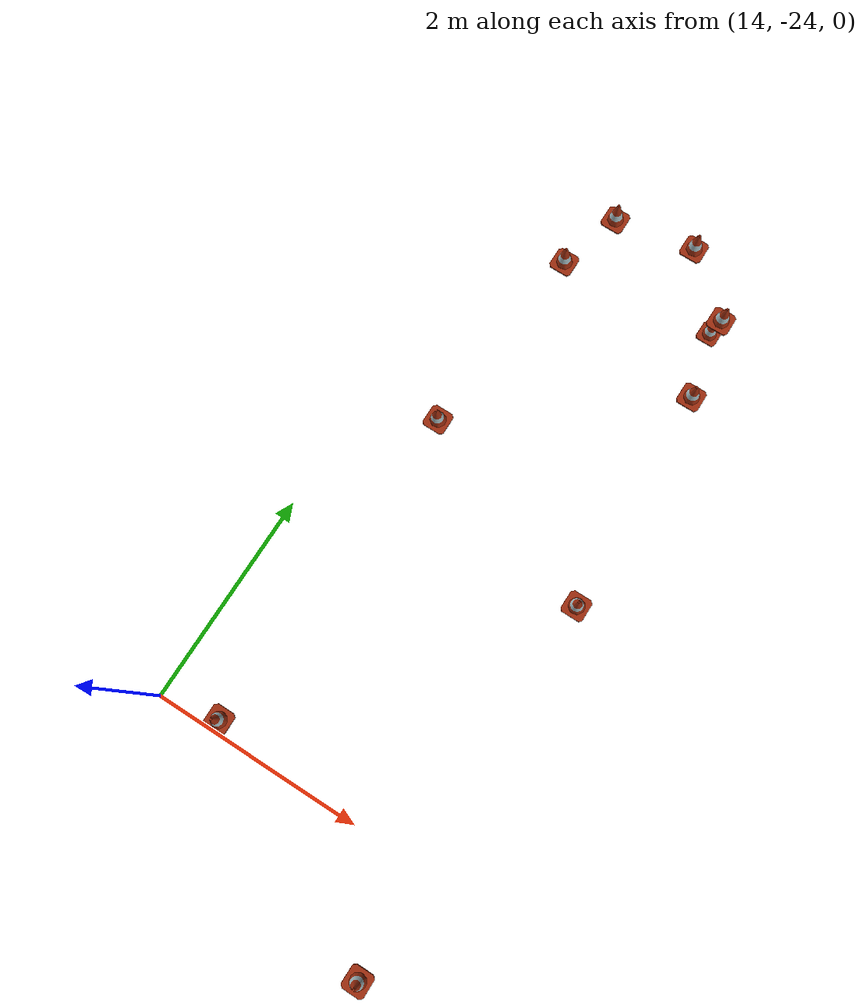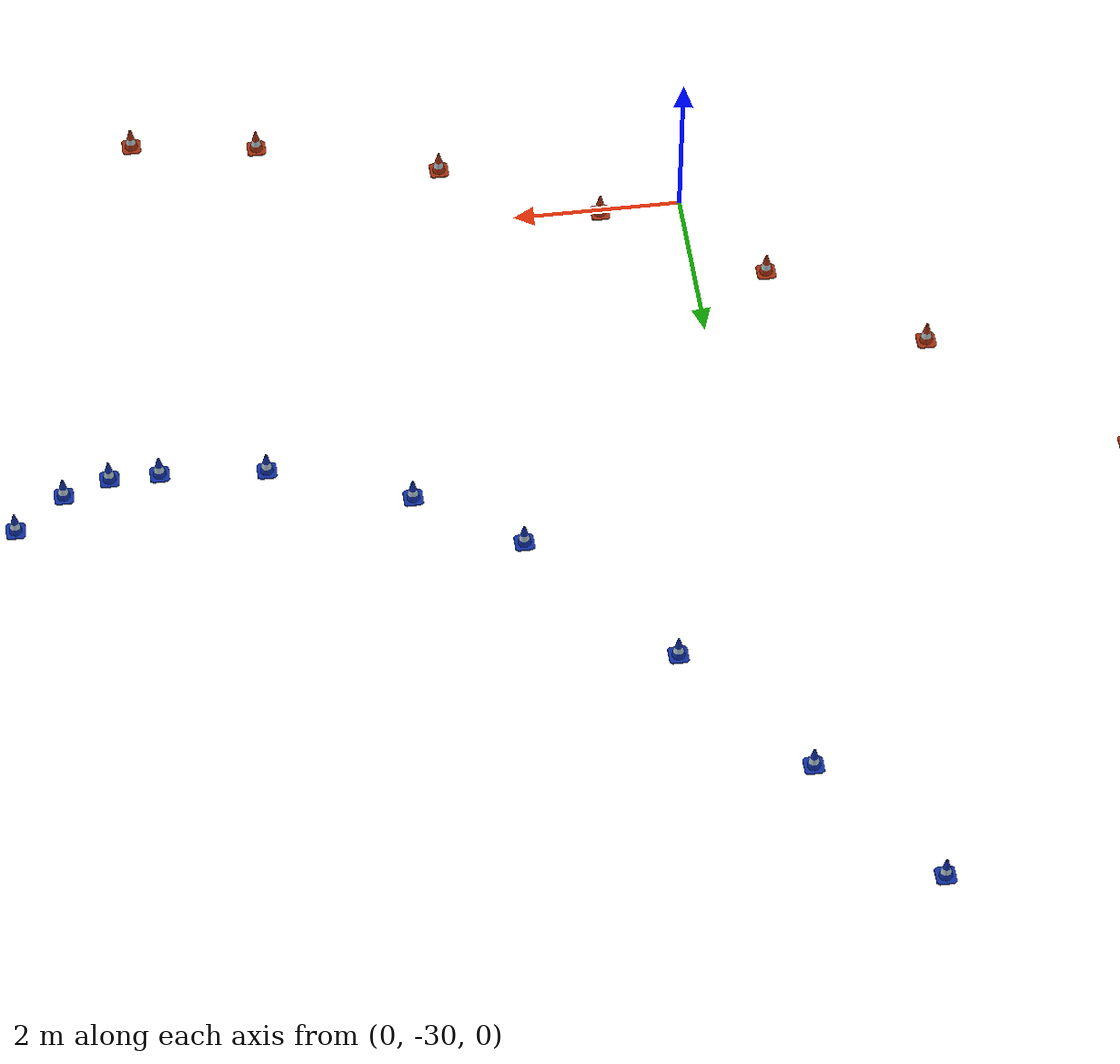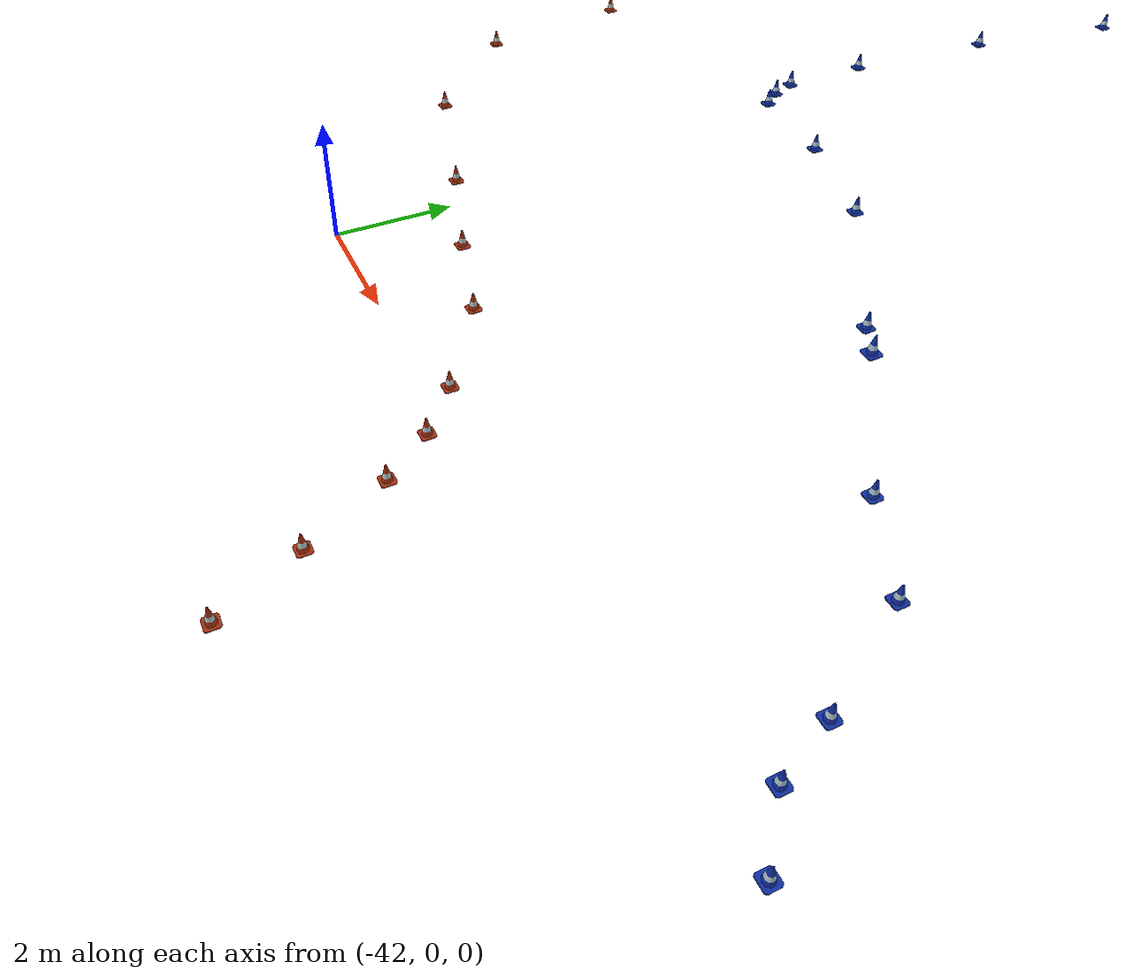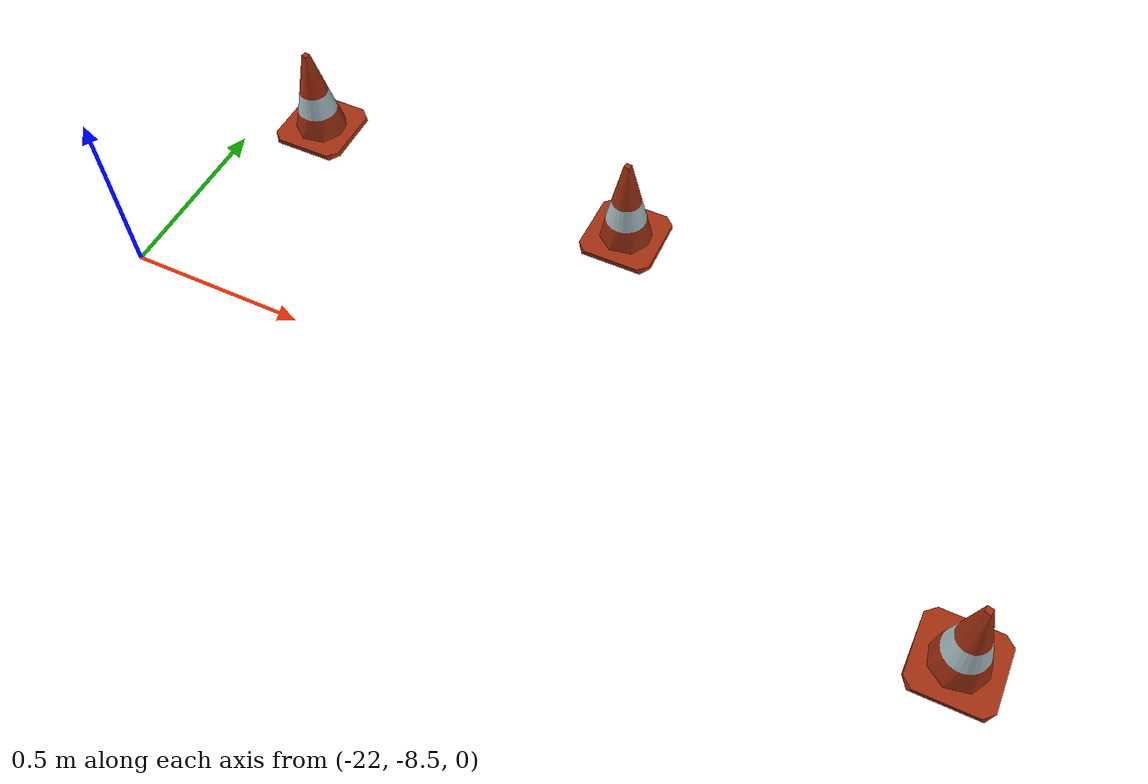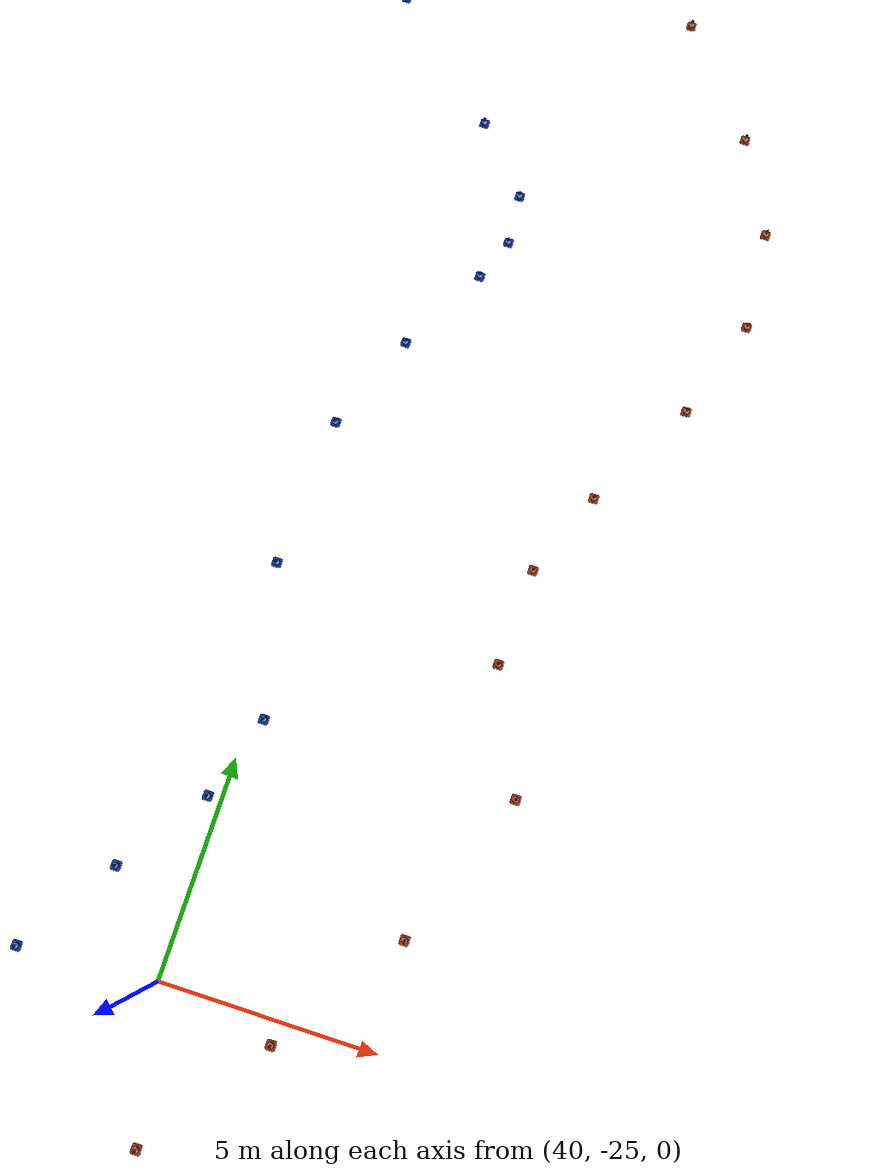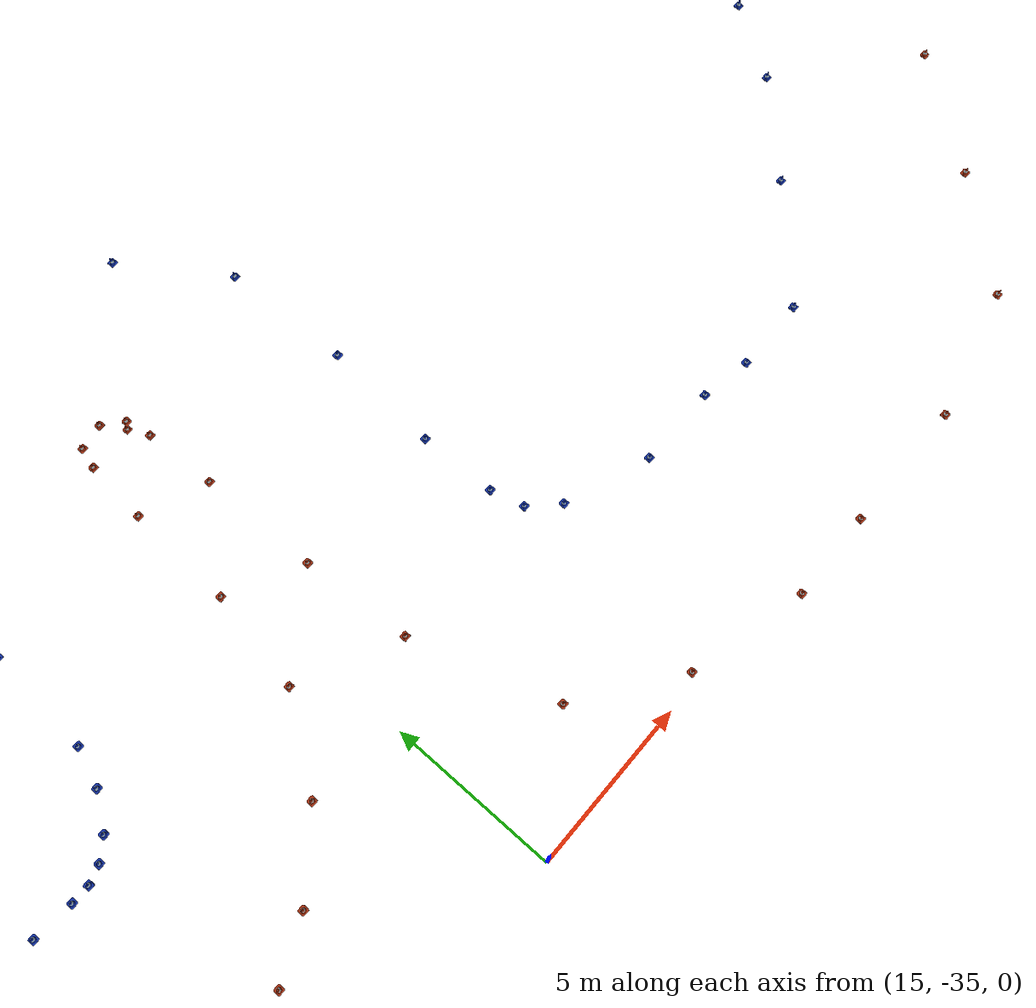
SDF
<?xml version='1.0'?>
<sdf version='1.6'>
  <model name='big_track'>
    <link name='link_2'>
      <pose frame=''>-45.6304 35.3629 -0.011962 0 -0 0</pose>
      <collision name="collision">
        <geometry>
          <mesh>
            <uri>model://eufs_description/meshes/cone_red.dae</uri>
          </mesh>
        </geometry>
      </collision>
      <visual name="visual">
        <geometry>
          <mesh>
            <uri>model://eufs_description/meshes/cone_red.dae</uri>
          </mesh>
        </geometry>
      </visual>
    </link>
    <link name='link_2_clone'>
      <pose frame=''>-40.927 32.5484 -0.011962 0 -0 0</pose>
      <collision name="collision">
        <geometry>
          <mesh>
            <uri>model://eufs_description/meshes/cone_blue.dae</uri>
          </mesh>
        </geometry>
      </collision>
      <visual name="visual">
        <geometry>
          <mesh>
            <uri>model://eufs_description/meshes/cone_blue.dae</uri>
          </mesh>
        </geometry>
      </visual>
    </link>
    <link name='link_2_clone_0'>
      <pose frame=''>-41.3526 38.5524 -0.011962 0 -0 0</pose>
      <collision name="collision">
        <geometry>
          <mesh>
            <uri>model://eufs_description/meshes/cone_red.dae</uri>
          </mesh>
        </geometry>
      </collision>
      <visual name="visual">
        <geometry>
          <mesh>
            <uri>model://eufs_description/meshes/cone_red.dae</uri>
          </mesh>
        </geometry>
      </visual>
    </link>
    <link name='link_2_clone_1'>
      <pose frame=''>-36.9867 38.7875 -0.011962 0 -0 0</pose>
      <collision name="collision">
        <geometry>
          <mesh>
            <uri>model://eufs_description/meshes/cone_red.dae</uri>
          </mesh>
        </geometry>
      </collision>
      <visual name="visual">
        <geometry>
          <mesh>
            <uri>model://eufs_description/meshes/cone_red.dae</uri>
          </mesh>
        </geometry>
      </visual>
    </link>
    <link name='link_2_clone_10'>
      <pose frame=''>-25.0953 38.6135 -0.011962 0 -0 0</pose>
      <collision name="collision">
        <geometry>
          <mesh>
            <uri>model://eufs_description/meshes/cone_red.dae</uri>
          </mesh>
        </geometry>
      </collision>
      <visual name="visual">
        <geometry>
          <mesh>
            <uri>model://eufs_description/meshes/cone_red.dae</uri>
          </mesh>
        </geometry>
      </visual>
    </link>
    <link name='link_2_clone_100'>
      <pose frame=''>19.4963 -14.6487 -0.011962 0 -0 0</pose>
      <collision name="collision">
        <geometry>
          <mesh>
            <uri>model://eufs_description/meshes/cone_blue.dae</uri>
          </mesh>
        </geometry>
      </collision>
      <visual name="visual">
        <geometry>
          <mesh>
            <uri>model://eufs_description/meshes/cone_blue.dae</uri>
          </mesh>
        </geometry>
      </visual>
    </link>
    <link name='link_2_clone_101'>
      <pose frame=''>16.4963 -12.6487 -0.011962 0 -0 0</pose>
      <collision name="collision">
        <geometry>
          <mesh>
            <uri>model://eufs_description/meshes/cone_blue.dae</uri>
          </mesh>
        </geometry>
      </collision>
      <visual name="visual">
        <geometry>
          <mesh>
            <uri>model://eufs_description/meshes/cone_blue.dae</uri>
          </mesh>
        </geometry>
      </visual>
    </link>
    <link name='link_2_clone_102'>
      <pose frame=''>12.4963 -13.1906 -0.011962 0 -0 0</pose>
      <collision name="collision">
        <geometry>
          <mesh>
            <uri>model://eufs_description/meshes/cone_blue.dae</uri>
          </mesh>
        </geometry>
      </collision>
      <visual name="visual">
        <geometry>
          <mesh>
            <uri>model://eufs_description/meshes/cone_blue.dae</uri>
          </mesh>
        </geometry>
      </visual>
    </link>
    <link name='link_2_clone_103'>
      <pose frame=''>10.4963 -17.068 -0.011962 0 -0 0</pose>
      <collision name="collision">
        <geometry>
          <mesh>
            <uri>model://eufs_description/meshes/cone_blue.dae</uri>
          </mesh>
        </geometry>
      </collision>
      <visual name="visual">
        <geometry>
          <mesh>
            <uri>model://eufs_description/meshes/cone_blue.dae</uri>
          </mesh>
        </geometry>
      </visual>
    </link>
    <link name='link_2_clone_104'>
      <pose frame=''>9.49626 -20.6487 -0.011962 0 -0 0</pose>
      <collision name="collision">
        <geometry>
          <mesh>
            <uri>model://eufs_description/meshes/cone_blue.dae</uri>
          </mesh>
        </geometry>
      </collision>
      <visual name="visual">
        <geometry>
          <mesh>
            <uri>model://eufs_description/meshes/cone_blue.dae</uri>
          </mesh>
        </geometry>
      </visual>
    </link>
    <link name='link_2_clone_105'>
      <pose frame=''>16.2958 -18.0044 -1.30935 0 -0 0</pose>
      <collision name="collision">
        <geometry>
          <mesh>
            <uri>model://eufs_description/meshes/cone_red.dae</uri>
          </mesh>
        </geometry>
      </collision>
      <visual name="visual">
        <geometry>
          <mesh>
            <uri>model://eufs_description/meshes/cone_red.dae</uri>
          </mesh>
        </geometry>
      </visual>
    </link>
    <link name='link_2_clone_106'>
      <pose frame=''>16.3557 -18.3977 -0.011962 0 -0 0</pose>
      <collision name="collision">
        <geometry>
          <mesh>
            <uri>model://eufs_description/meshes/cone_red.dae</uri>
          </mesh>
        </geometry>
      </collision>
      <visual name="visual">
        <geometry>
          <mesh>
            <uri>model://eufs_description/meshes/cone_red.dae</uri>
          </mesh>
        </geometry>
      </visual>
    </link>
    <link name='link_2_clone_107'>
      <pose frame=''>15.7784 -17.9091 -0.011962 0 -0 0</pose>
      <collision name="collision">
        <geometry>
          <mesh>
            <uri>model://eufs_description/meshes/cone_red.dae</uri>
          </mesh>
        </geometry>
      </collision>
      <visual name="visual">
        <geometry>
          <mesh>
            <uri>model://eufs_description/meshes/cone_red.dae</uri>
          </mesh>
        </geometry>
      </visual>
    </link>
    <link name='link_2_clone_108'>
      <pose frame=''>14.9935 -18.0515 -0.011962 0 -0 0</pose>
      <collision name="collision">
        <geometry>
          <mesh>
            <uri>model://eufs_description/meshes/cone_red.dae</uri>
          </mesh>
        </geometry>
      </collision>
      <visual name="visual">
        <geometry>
          <mesh>
            <uri>model://eufs_description/meshes/cone_red.dae</uri>
          </mesh>
        </geometry>
      </visual>
    </link>
    <link name='link_2_clone_109'>
      <pose frame=''>14.8069 -18.6802 -0.011962 0 -0 0</pose>
      <collision name="collision">
        <geometry>
          <mesh>
            <uri>model://eufs_description/meshes/cone_red.dae</uri>
          </mesh>
        </geometry>
      </collision>
      <visual name="visual">
        <geometry>
          <mesh>
            <uri>model://eufs_description/meshes/cone_red.dae</uri>
          </mesh>
        </geometry>
      </visual>
    </link>
    <link name='link_2_clone_11'>
      <pose frame=''>-21.6504 31.8567 -0.011962 0 -0 0</pose>
      <collision name="collision">
        <geometry>
          <mesh>
            <uri>model://eufs_description/meshes/cone_blue.dae</uri>
          </mesh>
        </geometry>
      </collision>
      <visual name="visual">
        <geometry>
          <mesh>
            <uri>model://eufs_description/meshes/cone_blue.dae</uri>
          </mesh>
        </geometry>
      </visual>
    </link>
    <link name='link_2_clone_110'>
      <pose frame=''>14.6399 -20.622 -0.011962 0 -0 0</pose>
      <collision name="collision">
        <geometry>
          <mesh>
            <uri>model://eufs_description/meshes/cone_red.dae</uri>
          </mesh>
        </geometry>
      </collision>
      <visual name="visual">
        <geometry>
          <mesh>
            <uri>model://eufs_description/meshes/cone_red.dae</uri>
          </mesh>
        </geometry>
      </visual>
    </link>
    <link name='link_2_clone_111'>
      <pose frame=''>9.2797 -23.9477 -0.011962 0 -0 0</pose>
      <collision name="collision">
        <geometry>
          <mesh>
            <uri>model://eufs_description/meshes/cone_blue.dae</uri>
          </mesh>
        </geometry>
      </collision>
      <visual name="visual">
        <geometry>
          <mesh>
            <uri>model://eufs_description/meshes/cone_blue.dae</uri>
          </mesh>
        </geometry>
      </visual>
    </link>
    <link name='link_2_clone_112'>
      <pose frame=''>14.5067 -23.9152 -0.011962 0 -0 0</pose>
      <collision name="collision">
        <geometry>
          <mesh>
            <uri>model://eufs_description/meshes/cone_red.dae</uri>
          </mesh>
        </geometry>
      </collision>
      <visual name="visual">
        <geometry>
          <mesh>
            <uri>model://eufs_description/meshes/cone_red.dae</uri>
          </mesh>
        </geometry>
      </visual>
    </link>
    <link name='link_2_clone_113'>
      <pose frame=''>8.85793 -25.0825 -0.011962 0 -0 0</pose>
      <collision name="collision">
        <geometry>
          <mesh>
            <uri>model://eufs_description/meshes/cone_blue.dae</uri>
          </mesh>
        </geometry>
      </collision>
      <visual name="visual">
        <geometry>
          <mesh>
            <uri>model://eufs_description/meshes/cone_blue.dae</uri>
          </mesh>
        </geometry>
      </visual>
    </link>
    <link name='link_2_clone_114'>
      <pose frame=''>13.9656 -26.9757 -0.011962 0 -0 0</pose>
      <collision name="collision">
        <geometry>
          <mesh>
            <uri>model://eufs_description/meshes/cone_red.dae</uri>
          </mesh>
        </geometry>
      </collision>
      <visual name="visual">
        <geometry>
          <mesh>
            <uri>model://eufs_description/meshes/cone_red.dae</uri>
          </mesh>
        </geometry>
      </visual>
    </link>
    <link name='link_2_clone_115'>
      <pose frame=''>7.60125 -26.4693 -0.011962 0 -0 0</pose>
      <collision name="collision">
        <geometry>
          <mesh>
            <uri>model://eufs_description/meshes/cone_blue.dae</uri>
          </mesh>
        </geometry>
      </collision>
      <visual name="visual">
        <geometry>
          <mesh>
            <uri>model://eufs_description/meshes/cone_blue.dae</uri>
          </mesh>
        </geometry>
      </visual>
    </link>
    <link name='link_2_clone_116'>
      <pose frame=''>12.2248 -29.4547 -0.011962 0 -0 0</pose>
      <collision name="collision">
        <geometry>
          <mesh>
            <uri>model://eufs_description/meshes/cone_red.dae</uri>
          </mesh>
        </geometry>
      </collision>
      <visual name="visual">
        <geometry>
          <mesh>
            <uri>model://eufs_description/meshes/cone_red.dae</uri>
          </mesh>
        </geometry>
      </visual>
    </link>
    <link name='link_2_clone_117'>
      <pose frame=''>8.17455 -26.0403 -0.011962 0 -0 0</pose>
      <collision name="collision">
        <geometry>
          <mesh>
            <uri>model://eufs_description/meshes/cone_blue.dae</uri>
          </mesh>
        </geometry>
      </collision>
      <visual name="visual">
        <geometry>
          <mesh>
            <uri>model://eufs_description/meshes/cone_blue.dae</uri>
          </mesh>
        </geometry>
      </visual>
    </link>
    <link name='link_2_clone_118'>
      <pose frame=''>10.1389 -31.1258 -0.011962 0 -0 0</pose>
      <collision name="collision">
        <geometry>
          <mesh>
            <uri>model://eufs_description/meshes/cone_red.dae</uri>
          </mesh>
        </geometry>
      </collision>
      <visual name="visual">
        <geometry>
          <mesh>
            <uri>model://eufs_description/meshes/cone_red.dae</uri>
          </mesh>
        </geometry>
      </visual>
    </link>
    <link name='link_2_clone_119'>
      <pose frame=''>6.49627 -26.6487 -0.011962 0 -0 0</pose>
      <collision name="collision">
        <geometry>
          <mesh>
            <uri>model://eufs_description/meshes/cone_blue.dae</uri>
          </mesh>
        </geometry>
      </collision>
      <visual name="visual">
        <geometry>
          <mesh>
            <uri>model://eufs_description/meshes/cone_blue.dae</uri>
          </mesh>
        </geometry>
      </visual>
    </link>
    <link name='link_2_clone_12'>
      <pose frame=''>-21.4112 37.9542 -0.011962 0 -0 0</pose>
      <collision name="collision">
        <geometry>
          <mesh>
            <uri>model://eufs_description/meshes/cone_red.dae</uri>
          </mesh>
        </geometry>
      </collision>
      <visual name="visual">
        <geometry>
          <mesh>
            <uri>model://eufs_description/meshes/cone_red.dae</uri>
          </mesh>
        </geometry>
      </visual>
    </link>
    <link name='link_2_clone_120'>
      <pose frame=''>8.38956 -31.962 -0.011962 0 -0 0</pose>
      <collision name="collision">
        <geometry>
          <mesh>
            <uri>model://eufs_description/meshes/cone_red.dae</uri>
          </mesh>
        </geometry>
      </collision>
      <visual name="visual">
        <geometry>
          <mesh>
            <uri>model://eufs_description/meshes/cone_red.dae</uri>
          </mesh>
        </geometry>
      </visual>
    </link>
    <link name='link_2_clone_121'>
      <pose frame=''>7.0684 -26.6487 -0.011962 0 -0 0</pose>
      <collision name="collision">
        <geometry>
          <mesh>
            <uri>model://eufs_description/meshes/cone_blue.dae</uri>
          </mesh>
        </geometry>
      </collision>
      <visual name="visual">
        <geometry>
          <mesh>
            <uri>model://eufs_description/meshes/cone_blue.dae</uri>
          </mesh>
        </geometry>
      </visual>
    </link>
    <link name='link_2_clone_122'>
      <pose frame=''>6.42516 -31.8667 -0.011962 0 -0 0</pose>
      <collision name="collision">
        <geometry>
          <mesh>
            <uri>model://eufs_description/meshes/cone_red.dae</uri>
          </mesh>
        </geometry>
      </collision>
      <visual name="visual">
        <geometry>
          <mesh>
            <uri>model://eufs_description/meshes/cone_red.dae</uri>
          </mesh>
        </geometry>
      </visual>
    </link>
    <link name='link_2_clone_123'>
      <pose frame=''>5.27775 -26.5447 -0.011962 0 -0 0</pose>
      <collision name="collision">
        <geometry>
          <mesh>
            <uri>model://eufs_description/meshes/cone_blue.dae</uri>
          </mesh>
        </geometry>
      </collision>
      <visual name="visual">
        <geometry>
          <mesh>
            <uri>model://eufs_description/meshes/cone_blue.dae</uri>
          </mesh>
        </geometry>
      </visual>
    </link>
    <link name='link_2_clone_124'>
      <pose frame=''>4.92793 -31.6487 -0.011962 0 -0 0</pose>
      <collision name="collision">
        <geometry>
          <mesh>
            <uri>model://eufs_description/meshes/cone_red.dae</uri>
          </mesh>
        </geometry>
      </collision>
      <visual name="visual">
        <geometry>
          <mesh>
            <uri>model://eufs_description/meshes/cone_red.dae</uri>
          </mesh>
        </geometry>
      </visual>
    </link>
    <link name='link_2_clone_125'>
      <pose frame=''>3.66717 -25.9442 -0.011962 0 -0 0</pose>
      <collision name="collision">
        <geometry>
          <mesh>
            <uri>model://eufs_description/meshes/cone_blue.dae</uri>
          </mesh>
        </geometry>
      </collision>
      <visual name="visual">
        <geometry>
          <mesh>
            <uri>model://eufs_description/meshes/cone_blue.dae</uri>
          </mesh>
        </geometry>
      </visual>
    </link>
    <link name='link_2_clone_126'>
      <pose frame=''>2.77998 -31.0149 -0.011962 0 -0 0</pose>
      <collision name="collision">
        <geometry>
          <mesh>
            <uri>model://eufs_description/meshes/cone_red.dae</uri>
          </mesh>
        </geometry>
      </collision>
      <visual name="visual">
        <geometry>
          <mesh>
            <uri>model://eufs_description/meshes/cone_red.dae</uri>
          </mesh>
        </geometry>
      </visual>
    </link>
    <link name='link_2_clone_127'>
      <pose frame=''>2.49627 -25.1453 -0.011962 0 -0 0</pose>
      <collision name="collision">
        <geometry>
          <mesh>
            <uri>model://eufs_description/meshes/cone_blue.dae</uri>
          </mesh>
        </geometry>
      </collision>
      <visual name="visual">
        <geometry>
          <mesh>
            <uri>model://eufs_description/meshes/cone_blue.dae</uri>
          </mesh>
        </geometry>
      </visual>
    </link>
    <link name='link_2_clone_128'>
      <pose frame=''>0.947282 -30.0934 -0.011962 0 -0 0</pose>
      <collision name="collision">
        <geometry>
          <mesh>
            <uri>model://eufs_description/meshes/cone_red.dae</uri>
          </mesh>
        </geometry>
      </collision>
      <visual name="visual">
        <geometry>
          <mesh>
            <uri>model://eufs_description/meshes/cone_red.dae</uri>
          </mesh>
        </geometry>
      </visual>
    </link>
    <link name='link_2_clone_129'>
      <pose frame=''>1.00574 -23.3676 -0.011962 0 -0 0</pose>
      <collision name="collision">
        <geometry>
          <mesh>
            <uri>model://eufs_description/meshes/cone_blue.dae</uri>
          </mesh>
        </geometry>
      </collision>
      <visual name="visual">
        <geometry>
          <mesh>
            <uri>model://eufs_description/meshes/cone_blue.dae</uri>
          </mesh>
        </geometry>
      </visual>
    </link>
    <link name='link_2_clone_13'>
      <pose frame=''>-19.3572 38.3138 -0.011962 0 -0 0</pose>
      <collision name="collision">
        <geometry>
          <mesh>
            <uri>model://eufs_description/meshes/cone_red.dae</uri>
          </mesh>
        </geometry>
      </collision>
      <visual name="visual">
        <geometry>
          <mesh>
            <uri>model://eufs_description/meshes/cone_red.dae</uri>
          </mesh>
        </geometry>
      </visual>
    </link>
    <link name='link_2_clone_130'>
      <pose frame=''>-0.872662 -28.9165 -0.011962 0 -0 0</pose>
      <collision name="collision">
        <geometry>
          <mesh>
            <uri>model://eufs_description/meshes/cone_red.dae</uri>
          </mesh>
        </geometry>
      </collision>
      <visual name="visual">
        <geometry>
          <mesh>
            <uri>model://eufs_description/meshes/cone_red.dae</uri>
          </mesh>
        </geometry>
      </visual>
    </link>
    <link name='link_2_clone_131'>
      <pose frame=''>-2.56202 -27.6299 -0.011962 0 -0 0</pose>
      <collision name="collision">
        <geometry>
          <mesh>
            <uri>model://eufs_description/meshes/cone_red.dae</uri>
          </mesh>
        </geometry>
      </collision>
      <visual name="visual">
        <geometry>
          <mesh>
            <uri>model://eufs_description/meshes/cone_red.dae</uri>
          </mesh>
        </geometry>
      </visual>
    </link>
    <link name='link_2_clone_132'>
      <pose frame=''>-0.235406 -21.7046 -0.011962 0 -0 0</pose>
      <collision name="collision">
        <geometry>
          <mesh>
            <uri>model://eufs_description/meshes/cone_blue.dae</uri>
          </mesh>
        </geometry>
      </collision>
      <visual name="visual">
        <geometry>
          <mesh>
            <uri>model://eufs_description/meshes/cone_blue.dae</uri>
          </mesh>
        </geometry>
      </visual>
    </link>
    <link name='link_2_clone_133'>
      <pose frame=''>-4.59462 -25.8097 -0.011962 0 -0 0</pose>
      <collision name="collision">
        <geometry>
          <mesh>
            <uri>model://eufs_description/meshes/cone_red.dae</uri>
          </mesh>
        </geometry>
      </collision>
      <visual name="visual">
        <geometry>
          <mesh>
            <uri>model://eufs_description/meshes/cone_red.dae</uri>
          </mesh>
        </geometry>
      </visual>
    </link>
    <link name='link_2_clone_134'>
      <pose frame=''>-1.3971 -20.1076 -0.011962 0 -0 0</pose>
      <collision name="collision">
        <geometry>
          <mesh>
            <uri>model://eufs_description/meshes/cone_blue.dae</uri>
          </mesh>
        </geometry>
      </collision>
      <visual name="visual">
        <geometry>
          <mesh>
            <uri>model://eufs_description/meshes/cone_blue.dae</uri>
          </mesh>
        </geometry>
      </visual>
    </link>
    <link name='link_2_clone_135'>
      <pose frame=''>-7.35063 -23.3456 -0.011962 0 -0 0</pose>
      <collision name="collision">
        <geometry>
          <mesh>
            <uri>model://eufs_description/meshes/cone_red.dae</uri>
          </mesh>
        </geometry>
      </collision>
      <visual name="visual">
        <geometry>
          <mesh>
            <uri>model://eufs_description/meshes/cone_red.dae</uri>
          </mesh>
        </geometry>
      </visual>
    </link>
    <link name='link_2_clone_136'>
      <pose frame=''>-3.88 -17.7651 -0.011962 0 -0 0</pose>
      <collision name="collision">
        <geometry>
          <mesh>
            <uri>model://eufs_description/meshes/cone_blue.dae</uri>
          </mesh>
        </geometry>
      </collision>
      <visual name="visual">
        <geometry>
          <mesh>
            <uri>model://eufs_description/meshes/cone_blue.dae</uri>
          </mesh>
        </geometry>
      </visual>
    </link>
    <link name='link_2_clone_137'>
      <pose frame=''>-6.16247 -14.9785 -0.011962 0 -0 0</pose>
      <collision name="collision">
        <geometry>
          <mesh>
            <uri>model://eufs_description/meshes/cone_blue.dae</uri>
          </mesh>
        </geometry>
      </collision>
      <visual name="visual">
        <geometry>
          <mesh>
            <uri>model://eufs_description/meshes/cone_blue.dae</uri>
          </mesh>
        </geometry>
      </visual>
    </link>
    <link name='link_2_clone_138'>
      <pose frame=''>-9.81672 -20.6798 -0.011962 0 -0 0</pose>
      <collision name="collision">
        <geometry>
          <mesh>
            <uri>model://eufs_description/meshes/cone_red.dae</uri>
          </mesh>
        </geometry>
      </collision>
      <visual name="visual">
        <geometry>
          <mesh>
            <uri>model://eufs_description/meshes/cone_red.dae</uri>
          </mesh>
        </geometry>
      </visual>
    </link>
    <link name='link_2_clone_139'>
      <pose frame=''>-8.41111 -12.5617 -0.011962 0 -0 0</pose>
      <collision name="collision">
        <geometry>
          <mesh>
            <uri>model://eufs_description/meshes/cone_blue.dae</uri>
          </mesh>
        </geometry>
      </collision>
      <visual name="visual">
        <geometry>
          <mesh>
            <uri>model://eufs_description/meshes/cone_blue.dae</uri>
          </mesh>
        </geometry>
      </visual>
    </link>
    <link name='link_2_clone_14'>
      <pose frame=''>-17.4728 32.5353 -0.011962 0 -0 0</pose>
      <collision name="collision">
        <geometry>
          <mesh>
            <uri>model://eufs_description/meshes/cone_blue.dae</uri>
          </mesh>
        </geometry>
      </collision>
      <visual name="visual">
        <geometry>
          <mesh>
            <uri>model://eufs_description/meshes/cone_blue.dae</uri>
          </mesh>
        </geometry>
      </visual>
    </link>
    <link name='link_2_clone_140'>
      <pose frame=''>-12.2741 -17.4998 -0.011962 0 -0 0</pose>
      <collision name="collision">
        <geometry>
          <mesh>
            <uri>model://eufs_description/meshes/cone_red.dae</uri>
          </mesh>
        </geometry>
      </collision>
      <visual name="visual">
        <geometry>
          <mesh>
            <uri>model://eufs_description/meshes/cone_red.dae</uri>
          </mesh>
        </geometry>
      </visual>
    </link>
    <link name='link_2_clone_141'>
      <pose frame=''>-14.1274 -15.4903 -0.011962 0 -0 0</pose>
      <collision name="collision">
        <geometry>
          <mesh>
            <uri>model://eufs_description/meshes/cone_red.dae</uri>
          </mesh>
        </geometry>
      </collision>
      <visual name="visual">
        <geometry>
          <mesh>
            <uri>model://eufs_description/meshes/cone_red.dae</uri>
          </mesh>
        </geometry>
      </visual>
    </link>
    <link name='link_2_clone_142'>
      <pose frame=''>-9.98623 -10.1263 -0.011962 0 -0 0</pose>
      <collision name="collision">
        <geometry>
          <mesh>
            <uri>model://eufs_description/meshes/cone_blue.dae</uri>
          </mesh>
        </geometry>
      </collision>
      <visual name="visual">
        <geometry>
          <mesh>
            <uri>model://eufs_description/meshes/cone_blue.dae</uri>
          </mesh>
        </geometry>
      </visual>
    </link>
    <link name='link_2_clone_143'>
      <pose frame=''>-16.4386 -13.0137 -0.011962 0 -0 0</pose>
      <collision name="collision">
        <geometry>
          <mesh>
            <uri>model://eufs_description/meshes/cone_red.dae</uri>
          </mesh>
        </geometry>
      </collision>
      <visual name="visual">
        <geometry>
          <mesh>
            <uri>model://eufs_description/meshes/cone_red.dae</uri>
          </mesh>
        </geometry>
      </visual>
    </link>
    <link name='link_2_clone_144'>
      <pose frame=''>-12.0133 -7.67523 -0.011962 0 -0 0</pose>
      <collision name="collision">
        <geometry>
          <mesh>
            <uri>model://eufs_description/meshes/cone_blue.dae</uri>
          </mesh>
        </geometry>
      </collision>
      <visual name="visual">
        <geometry>
          <mesh>
            <uri>model://eufs_description/meshes/cone_blue.dae</uri>
          </mesh>
        </geometry>
      </visual>
    </link>
    <link name='link_2_clone_145'>
      <pose frame=''>-18.398 -10.0858 -0.011962 0 -0 0</pose>
      <collision name="collision">
        <geometry>
          <mesh>
            <uri>model://eufs_description/meshes/cone_red.dae</uri>
          </mesh>
        </geometry>
      </collision>
      <visual name="visual">
        <geometry>
          <mesh>
            <uri>model://eufs_description/meshes/cone_red.dae</uri>
          </mesh>
        </geometry>
      </visual>
    </link>
    <link name='link_2_clone_146'>
      <pose frame=''>-14.145 -4.8647 -0.011962 0 -0 0</pose>
      <collision name="collision">
        <geometry>
          <mesh>
            <uri>model://eufs_description/meshes/cone_blue.dae</uri>
          </mesh>
        </geometry>
      </collision>
      <visual name="visual">
        <geometry>
          <mesh>
            <uri>model://eufs_description/meshes/cone_blue.dae</uri>
          </mesh>
        </geometry>
      </visual>
    </link>
    <link name='link_2_clone_147'>
      <pose frame=''>-19.6418 -8.60711 -0.011962 0 -0 0</pose>
      <collision name="collision">
        <geometry>
          <mesh>
            <uri>model://eufs_description/meshes/cone_red.dae</uri>
          </mesh>
        </geometry>
      </collision>
      <visual name="visual">
        <geometry>
          <mesh>
            <uri>model://eufs_description/meshes/cone_red.dae</uri>
          </mesh>
        </geometry>
      </visual>
    </link>
    <link name='link_2_clone_148'>
      <pose frame=''>-15.5037 -2.64873 -0.011962 0 -0 0</pose>
      <collision name="collision">
        <geometry>
          <mesh>
            <uri>model://eufs_description/meshes/cone_blue.dae</uri>
          </mesh>
        </geometry>
      </collision>
      <visual name="visual">
        <geometry>
          <mesh>
            <uri>model://eufs_description/meshes/cone_blue.dae</uri>
          </mesh>
        </geometry>
      </visual>
    </link>
    <link name='link_2_clone_149'>
      <pose frame=''>-18.5037 -0.648733 -0.011962 0 -0 0</pose>
      <collision name="collision">
        <geometry>
          <mesh>
            <uri>model://eufs_description/meshes/cone_blue.dae</uri>
          </mesh>
        </geometry>
      </collision>
      <visual name="visual">
        <geometry>
          <mesh>
            <uri>model://eufs_description/meshes/cone_blue.dae</uri>
          </mesh>
        </geometry>
      </visual>
    </link>
    <link name='link_2_clone_15'>
      <pose frame=''>-15.4942 39.9386 -0.011962 0 -0 0</pose>
      <collision name="collision">
        <geometry>
          <mesh>
            <uri>model://eufs_description/meshes/cone_red.dae</uri>
          </mesh>
        </geometry>
      </collision>
      <visual name="visual">
        <geometry>
          <mesh>
            <uri>model://eufs_description/meshes/cone_red.dae</uri>
          </mesh>
        </geometry>
      </visual>
    </link>
    <link name='link_2_clone_150'>
      <pose frame=''>-20.8802 -7.74288 -0.011962 0 -0 0</pose>
      <collision name="collision">
        <geometry>
          <mesh>
            <uri>model://eufs_description/meshes/cone_red.dae</uri>
          </mesh>
        </geometry>
      </collision>
      <visual name="visual">
        <geometry>
          <mesh>
            <uri>model://eufs_description/meshes/cone_red.dae</uri>
          </mesh>
        </geometry>
      </visual>
    </link>
    <link name='link_2_clone_151'>
      <pose frame=''>-21.0672 -0.178342 -0.011962 0 -0 0</pose>
      <collision name="collision">
        <geometry>
          <mesh>
            <uri>model://eufs_description/meshes/cone_blue.dae</uri>
          </mesh>
        </geometry>
      </collision>
      <visual name="visual">
        <geometry>
          <mesh>
            <uri>model://eufs_description/meshes/cone_blue.dae</uri>
          </mesh>
        </geometry>
      </visual>
    </link>
    <link name='link_2_clone_152'>
      <pose frame=''>-21.9291 -7.7359 -0.011962 0 -0 0</pose>
      <collision name="collision">
        <geometry>
          <mesh>
            <uri>model://eufs_description/meshes/cone_red.dae</uri>
          </mesh>
        </geometry>
      </collision>
      <visual name="visual">
        <geometry>
          <mesh>
            <uri>model://eufs_description/meshes/cone_red.dae</uri>
          </mesh>
        </geometry>
      </visual>
    </link>
    <link name='link_2_clone_153'>
      <pose frame=''>-23.6403 0.099577 -0.011962 0 -0 0</pose>
      <collision name="collision">
        <geometry>
          <mesh>
            <uri>model://eufs_description/meshes/cone_blue.dae</uri>
          </mesh>
        </geometry>
      </collision>
      <visual name="visual">
        <geometry>
          <mesh>
            <uri>model://eufs_description/meshes/cone_blue.dae</uri>
          </mesh>
        </geometry>
      </visual>
    </link>
    <link name='link_2_clone_154'>
      <pose frame=''>-23.7944 -7.64806 -0.011962 0 -0 0</pose>
      <collision name="collision">
        <geometry>
          <mesh>
            <uri>model://eufs_description/meshes/cone_red.dae</uri>
          </mesh>
        </geometry>
      </collision>
      <visual name="visual">
        <geometry>
          <mesh>
            <uri>model://eufs_description/meshes/cone_red.dae</uri>
          </mesh>
        </geometry>
      </visual>
    </link>
    <link name='link_2_clone_155'>
      <pose frame=''>-26.3761 0.157103 -0.011962 0 -0 0</pose>
      <collision name="collision">
        <geometry>
          <mesh>
            <uri>model://eufs_description/meshes/cone_blue.dae</uri>
          </mesh>
        </geometry>
      </collision>
      <visual name="visual">
        <geometry>
          <mesh>
            <uri>model://eufs_description/meshes/cone_blue.dae</uri>
          </mesh>
        </geometry>
      </visual>
    </link>
    <link name='link_2_clone_156'>
      <pose frame=''>-26.8416 -7.58556 -0.011962 0 -0 0</pose>
      <collision name="collision">
        <geometry>
          <mesh>
            <uri>model://eufs_description/meshes/cone_red.dae</uri>
          </mesh>
        </geometry>
      </collision>
      <visual name="visual">
        <geometry>
          <mesh>
            <uri>model://eufs_description/meshes/cone_red.dae</uri>
          </mesh>
        </geometry>
      </visual>
    </link>
    <link name='link_2_clone_157'>
      <pose frame=''>-29.1732 0.184986 -0.011962 0 -0 0</pose>
      <collision name="collision">
        <geometry>
          <mesh>
            <uri>model://eufs_description/meshes/cone_blue.dae</uri>
          </mesh>
        </geometry>
      </collision>
      <visual name="visual">
        <geometry>
          <mesh>
            <uri>model://eufs_description/meshes/cone_blue.dae</uri>
          </mesh>
        </geometry>
      </visual>
    </link>
    <link name='link_2_clone_158'>
      <pose frame=''>-29.5832 -7.53744 -0.011962 0 -0 0</pose>
      <collision name="collision">
        <geometry>
          <mesh>
            <uri>model://eufs_description/meshes/cone_red.dae</uri>
          </mesh>
        </geometry>
      </collision>
      <visual name="visual">
        <geometry>
          <mesh>
            <uri>model://eufs_description/meshes/cone_red.dae</uri>
          </mesh>
        </geometry>
      </visual>
    </link>
    <link name='link_2_clone_159'>
      <pose frame=''>-30.3725 0.399499 -0.011962 0 -0 0</pose>
      <collision name="collision">
        <geometry>
          <mesh>
            <uri>model://eufs_description/meshes/cone_blue.dae</uri>
          </mesh>
        </geometry>
      </collision>
      <visual name="visual">
        <geometry>
          <mesh>
            <uri>model://eufs_description/meshes/cone_blue.dae</uri>
          </mesh>
        </geometry>
      </visual>
    </link>
    <link name='link_2_clone_16'>
      <pose frame=''>-13.0358 34.4934 -0.011962 0 -0 0</pose>
      <collision name="collision">
        <geometry>
          <mesh>
            <uri>model://eufs_description/meshes/cone_blue.dae</uri>
          </mesh>
        </geometry>
      </collision>
      <visual name="visual">
        <geometry>
          <mesh>
            <uri>model://eufs_description/meshes/cone_blue.dae</uri>
          </mesh>
        </geometry>
      </visual>
    </link>
    <link name='link_2_clone_160'>
      <pose frame=''>-32.9132 -6.64873 -0.011962 0 -0 0</pose>
      <collision name="collision">
        <geometry>
          <mesh>
            <uri>model://eufs_description/meshes/cone_red.dae</uri>
          </mesh>
        </geometry>
      </collision>
      <visual name="visual">
        <geometry>
          <mesh>
            <uri>model://eufs_description/meshes/cone_red.dae</uri>
          </mesh>
        </geometry>
      </visual>
    </link>
    <link name='link_2_clone_161'>
      <pose frame=''>-31.5037 1.94376 -0.011962 0 -0 0</pose>
      <collision name="collision">
        <geometry>
          <mesh>
            <uri>model://eufs_description/meshes/cone_blue.dae</uri>
          </mesh>
        </geometry>
      </collision>
      <visual name="visual">
        <geometry>
          <mesh>
            <uri>model://eufs_description/meshes/cone_blue.dae</uri>
          </mesh>
        </geometry>
      </visual>
    </link>
    <link name='link_2_clone_162'>
      <pose frame=''>-35.5037 -3.64873 -0.011962 0 -0 0</pose>
      <collision name="collision">
        <geometry>
          <mesh>
            <uri>model://eufs_description/meshes/cone_red.dae</uri>
          </mesh>
        </geometry>
      </collision>
      <visual name="visual">
        <geometry>
          <mesh>
            <uri>model://eufs_description/meshes/cone_red.dae</uri>
          </mesh>
        </geometry>
      </visual>
    </link>
    <link name='link_2_clone_163'>
      <pose frame=''>-31.1129 1.04038 -0.011962 0 -0 0</pose>
      <collision name="collision">
        <geometry>
          <mesh>
            <uri>model://eufs_description/meshes/cone_blue.dae</uri>
          </mesh>
        </geometry>
      </collision>
      <visual name="visual">
        <geometry>
          <mesh>
            <uri>model://eufs_description/meshes/cone_blue.dae</uri>
          </mesh>
        </geometry>
      </visual>
    </link>
    <link name='link_2_clone_164'>
      <pose frame=''>-36.0935 -2.38086 -0.011962 0 -0 0</pose>
      <collision name="collision">
        <geometry>
          <mesh>
            <uri>model://eufs_description/meshes/cone_red.dae</uri>
          </mesh>
        </geometry>
      </collision>
      <visual name="visual">
        <geometry>
          <mesh>
            <uri>model://eufs_description/meshes/cone_red.dae</uri>
          </mesh>
        </geometry>
      </visual>
    </link>
    <link name='link_2_clone_165'>
      <pose frame=''>-37.2996 -0.285214 -0.011962 0 -0 0</pose>
      <collision name="collision">
        <geometry>
          <mesh>
            <uri>model://eufs_description/meshes/cone_red.dae</uri>
          </mesh>
        </geometry>
      </collision>
      <visual name="visual">
        <geometry>
          <mesh>
            <uri>model://eufs_description/meshes/cone_red.dae</uri>
          </mesh>
        </geometry>
      </visual>
    </link>
    <link name='link_2_clone_166'>
      <pose frame=''>-32.4042 3.57254 -0.011962 0 -0 0</pose>
      <collision name="collision">
        <geometry>
          <mesh>
            <uri>model://eufs_description/meshes/cone_blue.dae</uri>
          </mesh>
        </geometry>
      </collision>
      <visual name="visual">
        <geometry>
          <mesh>
            <uri>model://eufs_description/meshes/cone_blue.dae</uri>
          </mesh>
        </geometry>
      </visual>
    </link>
    <link name='link_2_clone_167'>
      <pose frame=''>-36.7331 -1.06243 -0.011962 0 -0 0</pose>
      <collision name="collision">
        <geometry>
          <mesh>
            <uri>model://eufs_description/meshes/cone_red.dae</uri>
          </mesh>
        </geometry>
      </collision>
      <visual name="visual">
        <geometry>
          <mesh>
            <uri>model://eufs_description/meshes/cone_red.dae</uri>
          </mesh>
        </geometry>
      </visual>
    </link>
    <link name='link_2_clone_168'>
      <pose frame=''>-34.9765 4.88639 1.23306 0 -0 0</pose>
      <collision name="collision">
        <geometry>
          <mesh>
            <uri>model://eufs_description/meshes/cone_blue.dae</uri>
          </mesh>
        </geometry>
      </collision>
      <visual name="visual">
        <geometry>
          <mesh>
            <uri>model://eufs_description/meshes/cone_blue.dae</uri>
          </mesh>
        </geometry>
      </visual>
    </link>
    <link name='link_2_clone_169'>
      <pose frame=''>-33.8082 4.33242 -0.011962 0 -0 0</pose>
      <collision name="collision">
        <geometry>
          <mesh>
            <uri>model://eufs_description/meshes/cone_blue.dae</uri>
          </mesh>
        </geometry>
      </collision>
      <visual name="visual">
        <geometry>
          <mesh>
            <uri>model://eufs_description/meshes/cone_blue.dae</uri>
          </mesh>
        </geometry>
      </visual>
    </link>
    <link name='link_2_clone_17'>
      <pose frame=''>-10.9162 42.0497 -0.011962 0 -0 0</pose>
      <collision name="collision">
        <geometry>
          <mesh>
            <uri>model://eufs_description/meshes/cone_red.dae</uri>
          </mesh>
        </geometry>
      </collision>
      <visual name="visual">
        <geometry>
          <mesh>
            <uri>model://eufs_description/meshes/cone_red.dae</uri>
          </mesh>
        </geometry>
      </visual>
    </link>
    <link name='link_2_clone_170'>
      <pose frame=''>-38.0309 0.351267 -0.011962 0 -0 0</pose>
      <collision name="collision">
        <geometry>
          <mesh>
            <uri>model://eufs_description/meshes/cone_red.dae</uri>
          </mesh>
        </geometry>
      </collision>
      <visual name="visual">
        <geometry>
          <mesh>
            <uri>model://eufs_description/meshes/cone_red.dae</uri>
          </mesh>
        </geometry>
      </visual>
    </link>
    <link name='link_2_clone_171'>
      <pose frame=''>-39.5037 1.35127 -0.011962 0 -0 0</pose>
      <collision name="collision">
        <geometry>
          <mesh>
            <uri>model://eufs_description/meshes/cone_red.dae</uri>
          </mesh>
        </geometry>
      </collision>
      <visual name="visual">
        <geometry>
          <mesh>
            <uri>model://eufs_description/meshes/cone_red.dae</uri>
          </mesh>
        </geometry>
      </visual>
    </link>
    <link name='link_2_clone_172'>
      <pose frame=''>-36.5037 6.35127 -0.011962 0 -0 0</pose>
      <collision name="collision">
        <geometry>
          <mesh>
            <uri>model://eufs_description/meshes/cone_blue.dae</uri>
          </mesh>
        </geometry>
      </collision>
      <visual name="visual">
        <geometry>
          <mesh>
            <uri>model://eufs_description/meshes/cone_blue.dae</uri>
          </mesh>
        </geometry>
      </visual>
    </link>
    <link name='link_2_clone_173'>
      <pose frame=''>-41.085 1.84053 -0.011962 0 -0 0</pose>
      <collision name="collision">
        <geometry>
          <mesh>
            <uri>model://eufs_description/meshes/cone_red.dae</uri>
          </mesh>
        </geometry>
      </collision>
      <visual name="visual">
        <geometry>
          <mesh>
            <uri>model://eufs_description/meshes/cone_red.dae</uri>
          </mesh>
        </geometry>
      </visual>
    </link>
    <link name='link_2_clone_174'>
      <pose frame=''>-39.0248 8.11018 -0.011962 0 -0 0</pose>
      <collision name="collision">
        <geometry>
          <mesh>
            <uri>model://eufs_description/meshes/cone_blue.dae</uri>
          </mesh>
        </geometry>
      </collision>
      <visual name="visual">
        <geometry>
          <mesh>
            <uri>model://eufs_description/meshes/cone_blue.dae</uri>
          </mesh>
        </geometry>
      </visual>
    </link>
    <link name='link_2_clone_175'>
      <pose frame=''>-42.9327 2.50575 -0.011962 0 -0 0</pose>
      <collision name="collision">
        <geometry>
          <mesh>
            <uri>model://eufs_description/meshes/cone_red.dae</uri>
          </mesh>
        </geometry>
      </collision>
      <visual name="visual">
        <geometry>
          <mesh>
            <uri>model://eufs_description/meshes/cone_red.dae</uri>
          </mesh>
        </geometry>
      </visual>
    </link>
    <link name='link_2_clone_176'>
      <pose frame=''>-40.9746 8.72215 -0.011962 0 -0 0</pose>
      <collision name="collision">
        <geometry>
          <mesh>
            <uri>model://eufs_description/meshes/cone_blue.dae</uri>
          </mesh>
        </geometry>
      </collision>
      <visual name="visual">
        <geometry>
          <mesh>
            <uri>model://eufs_description/meshes/cone_blue.dae</uri>
          </mesh>
        </geometry>
      </visual>
    </link>
    <link name='link_2_clone_177'>
      <pose frame=''>-45.5037 3.35127 -0.011962 0 -0 0</pose>
      <collision name="collision">
        <geometry>
          <mesh>
            <uri>model://eufs_description/meshes/cone_red.dae</uri>
          </mesh>
        </geometry>
      </collision>
      <visual name="visual">
        <geometry>
          <mesh>
            <uri>model://eufs_description/meshes/cone_red.dae</uri>
          </mesh>
        </geometry>
      </visual>
    </link>
    <link name='link_2_clone_178'>
      <pose frame=''>-47.5037 5.35127 -0.011962 0 -0 0</pose>
      <collision name="collision">
        <geometry>
          <mesh>
            <uri>model://eufs_description/meshes/cone_red.dae</uri>
          </mesh>
        </geometry>
      </collision>
      <visual name="visual">
        <geometry>
          <mesh>
            <uri>model://eufs_description/meshes/cone_red.dae</uri>
          </mesh>
        </geometry>
      </visual>
    </link>
    <link name='link_2_clone_179'>
      <pose frame=''>-47.9712 8.35127 -0.011962 0 -0 0</pose>
      <collision name="collision">
        <geometry>
          <mesh>
            <uri>model://eufs_description/meshes/cone_red.dae</uri>
          </mesh>
        </geometry>
      </collision>
      <visual name="visual">
        <geometry>
          <mesh>
            <uri>model://eufs_description/meshes/cone_red.dae</uri>
          </mesh>
        </geometry>
      </visual>
    </link>
    <link name='link_2_clone_18'>
      <pose frame=''>-8.95003 36.3694 -0.011962 0 -0 0</pose>
      <collision name="collision">
        <geometry>
          <mesh>
            <uri>model://eufs_description/meshes/cone_blue.dae</uri>
          </mesh>
        </geometry>
      </collision>
      <visual name="visual">
        <geometry>
          <mesh>
            <uri>model://eufs_description/meshes/cone_blue.dae</uri>
          </mesh>
        </geometry>
      </visual>
    </link>
    <link name='link_2_clone_180'>
      <pose frame=''>-42.7252 8.92131 -0.011962 0 -0 0</pose>
      <collision name="collision">
        <geometry>
          <mesh>
            <uri>model://eufs_description/meshes/cone_blue.dae</uri>
          </mesh>
        </geometry>
      </collision>
      <visual name="visual">
        <geometry>
          <mesh>
            <uri>model://eufs_description/meshes/cone_blue.dae</uri>
          </mesh>
        </geometry>
      </visual>
    </link>
    <link name='link_2_clone_181'>
      <pose frame=''>-42.9866 9.26927 -0.011962 0 -0 0</pose>
      <collision name="collision">
        <geometry>
          <mesh>
            <uri>model://eufs_description/meshes/cone_blue.dae</uri>
          </mesh>
        </geometry>
      </collision>
      <visual name="visual">
        <geometry>
          <mesh>
            <uri>model://eufs_description/meshes/cone_blue.dae</uri>
          </mesh>
        </geometry>
      </visual>
    </link>
    <link name='link_2_clone_182'>
      <pose frame=''>-43.1743 9.75299 -0.011962 0 -0 0</pose>
      <collision name="collision">
        <geometry>
          <mesh>
            <uri>model://eufs_description/meshes/cone_blue.dae</uri>
          </mesh>
        </geometry>
      </collision>
      <visual name="visual">
        <geometry>
          <mesh>
            <uri>model://eufs_description/meshes/cone_blue.dae</uri>
          </mesh>
        </geometry>
      </visual>
    </link>
    <link name='link_2_clone_183'>
      <pose frame=''>-43.2016 11.4237 -0.011962 0 -0 0</pose>
      <collision name="collision">
        <geometry>
          <mesh>
            <uri>model://eufs_description/meshes/cone_blue.dae</uri>
          </mesh>
        </geometry>
      </collision>
      <visual name="visual">
        <geometry>
          <mesh>
            <uri>model://eufs_description/meshes/cone_blue.dae</uri>
          </mesh>
        </geometry>
      </visual>
    </link>
    <link name='link_2_clone_184'>
      <pose frame=''>-47.9303 11.3604 -0.011962 0 -0 0</pose>
      <collision name="collision">
        <geometry>
          <mesh>
            <uri>model://eufs_description/meshes/cone_red.dae</uri>
          </mesh>
        </geometry>
      </collision>
      <visual name="visual">
        <geometry>
          <mesh>
            <uri>model://eufs_description/meshes/cone_red.dae</uri>
          </mesh>
        </geometry>
      </visual>
    </link>
    <link name='link_2_clone_185'>
      <pose frame=''>-47.8376 13.5665 -0.011962 0 -0 0</pose>
      <collision name="collision">
        <geometry>
          <mesh>
            <uri>model://eufs_description/meshes/cone_red.dae</uri>
          </mesh>
        </geometry>
      </collision>
      <visual name="visual">
        <geometry>
          <mesh>
            <uri>model://eufs_description/meshes/cone_red.dae</uri>
          </mesh>
        </geometry>
      </visual>
    </link>
    <link name='link_2_clone_186'>
      <pose frame=''>-42.9875 14.3643 -0.011962 0 -0 0</pose>
      <collision name="collision">
        <geometry>
          <mesh>
            <uri>model://eufs_description/meshes/cone_blue.dae</uri>
          </mesh>
        </geometry>
      </collision>
      <visual name="visual">
        <geometry>
          <mesh>
            <uri>model://eufs_description/meshes/cone_blue.dae</uri>
          </mesh>
        </geometry>
      </visual>
    </link>
    <link name='link_2_clone_187'>
      <pose frame=''>-47.5037 16.3513 -0.011962 0 -0 0</pose>
      <collision name="collision">
        <geometry>
          <mesh>
            <uri>model://eufs_description/meshes/cone_red.dae</uri>
          </mesh>
        </geometry>
      </collision>
      <visual name="visual">
        <geometry>
          <mesh>
            <uri>model://eufs_description/meshes/cone_red.dae</uri>
          </mesh>
        </geometry>
      </visual>
    </link>
    <link name='link_2_clone_188'>
      <pose frame=''>-42.5037 17.3513 -0.011962 0 -0 0</pose>
      <collision name="collision">
        <geometry>
          <mesh>
            <uri>model://eufs_description/meshes/cone_blue.dae</uri>
          </mesh>
        </geometry>
      </collision>
      <visual name="visual">
        <geometry>
          <mesh>
            <uri>model://eufs_description/meshes/cone_blue.dae</uri>
          </mesh>
        </geometry>
      </visual>
    </link>
    <link name='link_2_clone_189'>
      <pose frame=''>-47.1696 19.9034 -0.011962 0 -0 0</pose>
      <collision name="collision">
        <geometry>
          <mesh>
            <uri>model://eufs_description/meshes/cone_red.dae</uri>
          </mesh>
        </geometry>
      </collision>
      <visual name="visual">
        <geometry>
          <mesh>
            <uri>model://eufs_description/meshes/cone_red.dae</uri>
          </mesh>
        </geometry>
      </visual>
    </link>
    <link name='link_2_clone_19'>
      <pose frame=''>-6.22164 37.1138 -0.011962 0 -0 0</pose>
      <collision name="collision">
        <geometry>
          <mesh>
            <uri>model://eufs_description/meshes/cone_blue.dae</uri>
          </mesh>
        </geometry>
      </collision>
      <visual name="visual">
        <geometry>
          <mesh>
            <uri>model://eufs_description/meshes/cone_blue.dae</uri>
          </mesh>
        </geometry>
      </visual>
    </link>
    <link name='link_2_clone_190'>
      <pose frame=''>-42.2537 20.3541 -0.011962 0 -0 0</pose>
      <collision name="collision">
        <geometry>
          <mesh>
            <uri>model://eufs_description/meshes/cone_blue.dae</uri>
          </mesh>
        </geometry>
      </collision>
      <visual name="visual">
        <geometry>
          <mesh>
            <uri>model://eufs_description/meshes/cone_blue.dae</uri>
          </mesh>
        </geometry>
      </visual>
    </link>
    <link name='link_2_clone_191'>
      <pose frame=''>-47.2499 23.1868 -0.011962 0 -0 0</pose>
      <collision name="collision">
        <geometry>
          <mesh>
            <uri>model://eufs_description/meshes/cone_red.dae</uri>
          </mesh>
        </geometry>
      </collision>
      <visual name="visual">
        <geometry>
          <mesh>
            <uri>model://eufs_description/meshes/cone_red.dae</uri>
          </mesh>
        </geometry>
      </visual>
    </link>
    <link name='link_2_clone_192'>
      <pose frame=''>-42.3489 23.249 -0.011962 0 -0 0</pose>
      <collision name="collision">
        <geometry>
          <mesh>
            <uri>model://eufs_description/meshes/cone_blue.dae</uri>
          </mesh>
        </geometry>
      </collision>
      <visual name="visual">
        <geometry>
          <mesh>
            <uri>model://eufs_description/meshes/cone_blue.dae</uri>
          </mesh>
        </geometry>
      </visual>
    </link>
    <link name='link_2_clone_193'>
      <pose frame=''>-47.0494 26.3513 -0.011962 0 -0 0</pose>
      <collision name="collision">
        <geometry>
          <mesh>
            <uri>model://eufs_description/meshes/cone_red.dae</uri>
          </mesh>
        </geometry>
      </collision>
      <visual name="visual">
        <geometry>
          <mesh>
            <uri>model://eufs_description/meshes/cone_red.dae</uri>
          </mesh>
        </geometry>
      </visual>
    </link>
    <link name='link_2_clone_194'>
      <pose frame=''>-42.1556 25.8226 -0.011962 0 -0 0</pose>
      <collision name="collision">
        <geometry>
          <mesh>
            <uri>model://eufs_description/meshes/cone_blue.dae</uri>
          </mesh>
        </geometry>
      </collision>
      <visual name="visual">
        <geometry>
          <mesh>
            <uri>model://eufs_description/meshes/cone_blue.dae</uri>
          </mesh>
        </geometry>
      </visual>
    </link>
    <link name='link_2_clone_195'>
      <pose frame=''>-46.5037 29.929 -0.011962 0 -0 0</pose>
      <collision name="collision">
        <geometry>
          <mesh>
            <uri>model://eufs_description/meshes/cone_red.dae</uri>
          </mesh>
        </geometry>
      </collision>
      <visual name="visual">
        <geometry>
          <mesh>
            <uri>model://eufs_description/meshes/cone_red.dae</uri>
          </mesh>
        </geometry>
      </visual>
    </link>
    <link name='link_2_clone_196'>
      <pose frame=''>-41.8296 28.9371 -0.011962 0 -0 0</pose>
      <collision name="collision">
        <geometry>
          <mesh>
            <uri>model://eufs_description/meshes/cone_blue.dae</uri>
          </mesh>
        </geometry>
      </collision>
      <visual name="visual">
        <geometry>
          <mesh>
            <uri>model://eufs_description/meshes/cone_blue.dae</uri>
          </mesh>
        </geometry>
      </visual>
    </link>
    <link name='link_2_clone_197'>
      <pose frame=''>-46.335 32.6887 -0.011962 0 -0 0</pose>
      <collision name="collision">
        <geometry>
          <mesh>
            <uri>model://eufs_description/meshes/cone_red.dae</uri>
          </mesh>
        </geometry>
      </collision>
      <visual name="visual">
        <geometry>
          <mesh>
            <uri>model://eufs_description/meshes/cone_red.dae</uri>
          </mesh>
        </geometry>
      </visual>
    </link>
    <link name='link_2_clone_198'>
      <pose frame=''>-41.6281 31.1207 -0.011962 0 -0 0</pose>
      <collision name="collision">
        <geometry>
          <mesh>
            <uri>model://eufs_description/meshes/cone_blue.dae</uri>
          </mesh>
        </geometry>
      </collision>
      <visual name="visual">
        <geometry>
          <mesh>
            <uri>model://eufs_description/meshes/cone_blue.dae</uri>
          </mesh>
        </geometry>
      </visual>
    </link>
    <link name='link_2_clone_2'>
      <pose frame=''>-36.8154 32.7846 -0.011962 0 -0 0</pose>
      <collision name="collision">
        <geometry>
          <mesh>
            <uri>model://eufs_description/meshes/cone_blue.dae</uri>
          </mesh>
        </geometry>
      </collision>
      <visual name="visual">
        <geometry>
          <mesh>
            <uri>model://eufs_description/meshes/cone_blue.dae</uri>
          </mesh>
        </geometry>
      </visual>
    </link>
    <link name='link_2_clone_20'>
      <pose frame=''>-5.87614 43.1801 -0.011962 0 -0 0</pose>
      <collision name="collision">
        <geometry>
          <mesh>
            <uri>model://eufs_description/meshes/cone_red.dae</uri>
          </mesh>
        </geometry>
      </collision>
      <visual name="visual">
        <geometry>
          <mesh>
            <uri>model://eufs_description/meshes/cone_red.dae</uri>
          </mesh>
        </geometry>
      </visual>
    </link>
    <link name='link_2_clone_21'>
      <pose frame=''>-0.557809 41.4811 -0.011962 0 -0 0</pose>
      <collision name="collision">
        <geometry>
          <mesh>
            <uri>model://eufs_description/meshes/cone_red.dae</uri>
          </mesh>
        </geometry>
      </collision>
      <visual name="visual">
        <geometry>
          <mesh>
            <uri>model://eufs_description/meshes/cone_red.dae</uri>
          </mesh>
        </geometry>
      </visual>
    </link>
    <link name='link_2_clone_22'>
      <pose frame=''>-2.9041 35.93 -0.011962 0 -0 0</pose>
      <collision name="collision">
        <geometry>
          <mesh>
            <uri>model://eufs_description/meshes/cone_blue.dae</uri>
          </mesh>
        </geometry>
      </collision>
      <visual name="visual">
        <geometry>
          <mesh>
            <uri>model://eufs_description/meshes/cone_blue.dae</uri>
          </mesh>
        </geometry>
      </visual>
    </link>
    <link name='link_2_clone_23'>
      <pose frame=''>3.46296 39.3787 -0.011962 0 -0 0</pose>
      <collision name="collision">
        <geometry>
          <mesh>
            <uri>model://eufs_description/meshes/cone_red.dae</uri>
          </mesh>
        </geometry>
      </collision>
      <visual name="visual">
        <geometry>
          <mesh>
            <uri>model://eufs_description/meshes/cone_red.dae</uri>
          </mesh>
        </geometry>
      </visual>
    </link>
    <link name='link_2_clone_24'>
      <pose frame=''>0.566565 34.0277 -0.011962 0 -0 0</pose>
      <collision name="collision">
        <geometry>
          <mesh>
            <uri>model://eufs_description/meshes/cone_blue.dae</uri>
          </mesh>
        </geometry>
      </collision>
      <visual name="visual">
        <geometry>
          <mesh>
            <uri>model://eufs_description/meshes/cone_blue.dae</uri>
          </mesh>
        </geometry>
      </visual>
    </link>
    <link name='link_2_clone_25'>
      <pose frame=''>4.31752 32.0265 -0.011962 0 -0 0</pose>
      <collision name="collision">
        <geometry>
          <mesh>
            <uri>model://eufs_description/meshes/cone_blue.dae</uri>
          </mesh>
        </geometry>
      </collision>
      <visual name="visual">
        <geometry>
          <mesh>
            <uri>model://eufs_description/meshes/cone_blue.dae</uri>
          </mesh>
        </geometry>
      </visual>
    </link>
    <link name='link_2_clone_26'>
      <pose frame=''>7.19651 37.3911 -0.011962 0 -0 0</pose>
      <collision name="collision">
        <geometry>
          <mesh>
            <uri>model://eufs_description/meshes/cone_red.dae</uri>
          </mesh>
        </geometry>
      </collision>
      <visual name="visual">
        <geometry>
          <mesh>
            <uri>model://eufs_description/meshes/cone_red.dae</uri>
          </mesh>
        </geometry>
      </visual>
    </link>
    <link name='link_2_clone_27'>
      <pose frame=''>8.27062 29.9648 2.44478 0 -0 0</pose>
      <collision name="collision">
        <geometry>
          <mesh>
            <uri>model://eufs_description/meshes/cone_blue.dae</uri>
          </mesh>
        </geometry>
      </collision>
      <visual name="visual">
        <geometry>
          <mesh>
            <uri>model://eufs_description/meshes/cone_blue.dae</uri>
          </mesh>
        </geometry>
      </visual>
    </link>
    <link name='link_2_clone_28'>
      <pose frame=''>10.9069 35.3903 -0.011962 0 -0 0</pose>
      <collision name="collision">
        <geometry>
          <mesh>
            <uri>model://eufs_description/meshes/cone_red.dae</uri>
          </mesh>
        </geometry>
      </collision>
      <visual name="visual">
        <geometry>
          <mesh>
            <uri>model://eufs_description/meshes/cone_red.dae</uri>
          </mesh>
        </geometry>
      </visual>
    </link>
    <link name='link_2_clone_29'>
      <pose frame=''>11.8081 27.9783 -0.011962 0 -0 0</pose>
      <collision name="collision">
        <geometry>
          <mesh>
            <uri>model://eufs_description/meshes/cone_blue.dae</uri>
          </mesh>
        </geometry>
      </collision>
      <visual name="visual">
        <geometry>
          <mesh>
            <uri>model://eufs_description/meshes/cone_blue.dae</uri>
          </mesh>
        </geometry>
      </visual>
    </link>
    <link name='link_2_clone_3'>
      <pose frame=''>-32.6866 39.0355 -0.011962 0 -0 0</pose>
      <collision name="collision">
        <geometry>
          <mesh>
            <uri>model://eufs_description/meshes/cone_red.dae</uri>
          </mesh>
        </geometry>
      </collision>
      <visual name="visual">
        <geometry>
          <mesh>
            <uri>model://eufs_description/meshes/cone_red.dae</uri>
          </mesh>
        </geometry>
      </visual>
    </link>
    <link name='link_2_clone_30'>
      <pose frame=''>14.6284 33.3781 -0.011962 0 -0 0</pose>
      <collision name="collision">
        <geometry>
          <mesh>
            <uri>model://eufs_description/meshes/cone_red.dae</uri>
          </mesh>
        </geometry>
      </collision>
      <visual name="visual">
        <geometry>
          <mesh>
            <uri>model://eufs_description/meshes/cone_red.dae</uri>
          </mesh>
        </geometry>
      </visual>
    </link>
    <link name='link_2_clone_31'>
      <pose frame=''>15.4514 26.1157 -0.011962 0 -0 0</pose>
      <collision name="collision">
        <geometry>
          <mesh>
            <uri>model://eufs_description/meshes/cone_blue.dae</uri>
          </mesh>
        </geometry>
      </collision>
      <visual name="visual">
        <geometry>
          <mesh>
            <uri>model://eufs_description/meshes/cone_blue.dae</uri>
          </mesh>
        </geometry>
      </visual>
    </link>
    <link name='link_2_clone_32'>
      <pose frame=''>18.3222 31.3339 -0.011962 0 -0 0</pose>
      <collision name="collision">
        <geometry>
          <mesh>
            <uri>model://eufs_description/meshes/cone_red.dae</uri>
          </mesh>
        </geometry>
      </collision>
      <visual name="visual">
        <geometry>
          <mesh>
            <uri>model://eufs_description/meshes/cone_red.dae</uri>
          </mesh>
        </geometry>
      </visual>
    </link>
    <link name='link_2_clone_33'>
      <pose frame=''>19.1615 24.1361 -0.011962 0 -0 0</pose>
      <collision name="collision">
        <geometry>
          <mesh>
            <uri>model://eufs_description/meshes/cone_blue.dae</uri>
          </mesh>
        </geometry>
      </collision>
      <visual name="visual">
        <geometry>
          <mesh>
            <uri>model://eufs_description/meshes/cone_blue.dae</uri>
          </mesh>
        </geometry>
      </visual>
    </link>
    <link name='link_2_clone_34'>
      <pose frame=''>22.0805 29.3513 -0.011962 0 -0 0</pose>
      <collision name="collision">
        <geometry>
          <mesh>
            <uri>model://eufs_description/meshes/cone_red.dae</uri>
          </mesh>
        </geometry>
      </collision>
      <visual name="visual">
        <geometry>
          <mesh>
            <uri>model://eufs_description/meshes/cone_red.dae</uri>
          </mesh>
        </geometry>
      </visual>
    </link>
    <link name='link_2_clone_35'>
      <pose frame=''>22.9637 22.065 -0.011962 0 -0 0</pose>
      <collision name="collision">
        <geometry>
          <mesh>
            <uri>model://eufs_description/meshes/cone_blue.dae</uri>
          </mesh>
        </geometry>
      </collision>
      <visual name="visual">
        <geometry>
          <mesh>
            <uri>model://eufs_description/meshes/cone_blue.dae</uri>
          </mesh>
        </geometry>
      </visual>
    </link>
    <link name='link_2_clone_36'>
      <pose frame=''>25.803 27.3338 -0.011962 0 -0 0</pose>
      <collision name="collision">
        <geometry>
          <mesh>
            <uri>model://eufs_description/meshes/cone_red.dae</uri>
          </mesh>
        </geometry>
      </collision>
      <visual name="visual">
        <geometry>
          <mesh>
            <uri>model://eufs_description/meshes/cone_red.dae</uri>
          </mesh>
        </geometry>
      </visual>
    </link>
    <link name='link_2_clone_37'>
      <pose frame=''>26.5701 20.1937 -0.011962 0 -0 0</pose>
      <collision name="collision">
        <geometry>
          <mesh>
            <uri>model://eufs_description/meshes/cone_blue.dae</uri>
          </mesh>
        </geometry>
      </collision>
      <visual name="visual">
        <geometry>
          <mesh>
            <uri>model://eufs_description/meshes/cone_blue.dae</uri>
          </mesh>
        </geometry>
      </visual>
    </link>
    <link name='link_2_clone_38'>
      <pose frame=''>29.691 25.2616 -0.011962 0 -0 0</pose>
      <collision name="collision">
        <geometry>
          <mesh>
            <uri>model://eufs_description/meshes/cone_red.dae</uri>
          </mesh>
        </geometry>
      </collision>
      <visual name="visual">
        <geometry>
          <mesh>
            <uri>model://eufs_description/meshes/cone_red.dae</uri>
          </mesh>
        </geometry>
      </visual>
    </link>
    <link name='link_2_clone_39'>
      <pose frame=''>27.3319 19.4918 -0.011962 0 -0 0</pose>
      <collision name="collision">
        <geometry>
          <mesh>
            <uri>model://eufs_description/meshes/cone_blue.dae</uri>
          </mesh>
        </geometry>
      </collision>
      <visual name="visual">
        <geometry>
          <mesh>
            <uri>model://eufs_description/meshes/cone_blue.dae</uri>
          </mesh>
        </geometry>
      </visual>
    </link>
    <link name='link_2_clone_4'>
      <pose frame=''>-32.4264 32.9858 -0.011962 0 -0 0</pose>
      <collision name="collision">
        <geometry>
          <mesh>
            <uri>model://eufs_description/meshes/cone_blue.dae</uri>
          </mesh>
        </geometry>
      </collision>
      <visual name="visual">
        <geometry>
          <mesh>
            <uri>model://eufs_description/meshes/cone_blue.dae</uri>
          </mesh>
        </geometry>
      </visual>
    </link>
    <link name='link_2_clone_40'>
      <pose frame=''>31.2916 24.0056 -0.011962 0 -0 0</pose>
      <collision name="collision">
        <geometry>
          <mesh>
            <uri>model://eufs_description/meshes/cone_red.dae</uri>
          </mesh>
        </geometry>
      </collision>
      <visual name="visual">
        <geometry>
          <mesh>
            <uri>model://eufs_description/meshes/cone_red.dae</uri>
          </mesh>
        </geometry>
      </visual>
    </link>
    <link name='link_2_clone_41'>
      <pose frame=''>29.9958 17.1566 -0.011962 0 -0 0</pose>
      <collision name="collision">
        <geometry>
          <mesh>
            <uri>model://eufs_description/meshes/cone_blue.dae</uri>
          </mesh>
        </geometry>
      </collision>
      <visual name="visual">
        <geometry>
          <mesh>
            <uri>model://eufs_description/meshes/cone_blue.dae</uri>
          </mesh>
        </geometry>
      </visual>
    </link>
    <link name='link_2_clone_42'>
      <pose frame=''>34.1696 21.3641 -0.011962 0 -0 0</pose>
      <collision name="collision">
        <geometry>
          <mesh>
            <uri>model://eufs_description/meshes/cone_red.dae</uri>
          </mesh>
        </geometry>
      </collision>
      <visual name="visual">
        <geometry>
          <mesh>
            <uri>model://eufs_description/meshes/cone_red.dae</uri>
          </mesh>
        </geometry>
      </visual>
    </link>
    <link name='link_2_clone_43'>
      <pose frame=''>32.598 14.2564 -0.011962 0 -0 0</pose>
      <collision name="collision">
        <geometry>
          <mesh>
            <uri>model://eufs_description/meshes/cone_blue.dae</uri>
          </mesh>
        </geometry>
      </collision>
      <visual name="visual">
        <geometry>
          <mesh>
            <uri>model://eufs_description/meshes/cone_blue.dae</uri>
          </mesh>
        </geometry>
      </visual>
    </link>
    <link name='link_2_clone_44'>
      <pose frame=''>37.5243 17.782 -0.011962 0 -0 0</pose>
      <collision name="collision">
        <geometry>
          <mesh>
            <uri>model://eufs_description/meshes/cone_red.dae</uri>
          </mesh>
        </geometry>
      </collision>
      <visual name="visual">
        <geometry>
          <mesh>
            <uri>model://eufs_description/meshes/cone_red.dae</uri>
          </mesh>
        </geometry>
      </visual>
    </link>
    <link name='link_2_clone_45'>
      <pose frame=''>39.7564 13.5821 -0.011962 0 -0 0</pose>
      <collision name="collision">
        <geometry>
          <mesh>
            <uri>model://eufs_description/meshes/cone_red.dae</uri>
          </mesh>
        </geometry>
      </collision>
      <visual name="visual">
        <geometry>
          <mesh>
            <uri>model://eufs_description/meshes/cone_red.dae</uri>
          </mesh>
        </geometry>
      </visual>
    </link>
    <link name='link_2_clone_46'>
      <pose frame=''>34.044 11.6356 -0.011962 0 -0 0</pose>
      <collision name="collision">
        <geometry>
          <mesh>
            <uri>model://eufs_description/meshes/cone_blue.dae</uri>
          </mesh>
        </geometry>
      </collision>
      <visual name="visual">
        <geometry>
          <mesh>
            <uri>model://eufs_description/meshes/cone_blue.dae</uri>
          </mesh>
        </geometry>
      </visual>
    </link>
    <link name='link_2_clone_47'>
      <pose frame=''>40.4531 9.83505 -0.011962 0 -0 0</pose>
      <collision name="collision">
        <geometry>
          <mesh>
            <uri>model://eufs_description/meshes/cone_red.dae</uri>
          </mesh>
        </geometry>
      </collision>
      <visual name="visual">
        <geometry>
          <mesh>
            <uri>model://eufs_description/meshes/cone_red.dae</uri>
          </mesh>
        </geometry>
      </visual>
    </link>
    <link name='link_2_clone_48'>
      <pose frame=''>34.4557 9.00244 -0.011962 0 -0 0</pose>
      <collision name="collision">
        <geometry>
          <mesh>
            <uri>model://eufs_description/meshes/cone_blue.dae</uri>
          </mesh>
        </geometry>
      </collision>
      <visual name="visual">
        <geometry>
          <mesh>
            <uri>model://eufs_description/meshes/cone_blue.dae</uri>
          </mesh>
        </geometry>
      </visual>
    </link>
    <link name='link_2_clone_49'>
      <pose frame=''>40.8385 7.03441 -0.011962 0 -0 0</pose>
      <collision name="collision">
        <geometry>
          <mesh>
            <uri>model://eufs_description/meshes/cone_red.dae</uri>
          </mesh>
        </geometry>
      </collision>
      <visual name="visual">
        <geometry>
          <mesh>
            <uri>model://eufs_description/meshes/cone_red.dae</uri>
          </mesh>
        </geometry>
      </visual>
    </link>
    <link name='link_2_clone_5'>
      <pose frame=''>-31.6469 39.0471 -0.011962 0 -0 0</pose>
      <collision name="collision">
        <geometry>
          <mesh>
            <uri>model://eufs_description/meshes/cone_red.dae</uri>
          </mesh>
        </geometry>
      </collision>
      <visual name="visual">
        <geometry>
          <mesh>
            <uri>model://eufs_description/meshes/cone_red.dae</uri>
          </mesh>
        </geometry>
      </visual>
    </link>
    <link name='link_2_clone_50'>
      <pose frame=''>34.7884 5.92064 -0.011962 0 -0 0</pose>
      <collision name="collision">
        <geometry>
          <mesh>
            <uri>model://eufs_description/meshes/cone_blue.dae</uri>
          </mesh>
        </geometry>
      </collision>
      <visual name="visual">
        <geometry>
          <mesh>
            <uri>model://eufs_description/meshes/cone_blue.dae</uri>
          </mesh>
        </geometry>
      </visual>
    </link>
    <link name='link_2_clone_51'>
      <pose frame=''>41.3157 4.96992 -0.011962 0 -0 0</pose>
      <collision name="collision">
        <geometry>
          <mesh>
            <uri>model://eufs_description/meshes/cone_red.dae</uri>
          </mesh>
        </geometry>
      </collision>
      <visual name="visual">
        <geometry>
          <mesh>
            <uri>model://eufs_description/meshes/cone_red.dae</uri>
          </mesh>
        </geometry>
      </visual>
    </link>
    <link name='link_2_clone_52'>
      <pose frame=''>35.7285 2.59291 -0.011962 0 -0 0</pose>
      <collision name="collision">
        <geometry>
          <mesh>
            <uri>model://eufs_description/meshes/cone_blue.dae</uri>
          </mesh>
        </geometry>
      </collision>
      <visual name="visual">
        <geometry>
          <mesh>
            <uri>model://eufs_description/meshes/cone_blue.dae</uri>
          </mesh>
        </geometry>
      </visual>
    </link>
    <link name='link_2_clone_53'>
      <pose frame=''>42.3663 3.11414 -0.011962 0 -0 0</pose>
      <collision name="collision">
        <geometry>
          <mesh>
            <uri>model://eufs_description/meshes/cone_red.dae</uri>
          </mesh>
        </geometry>
      </collision>
      <visual name="visual">
        <geometry>
          <mesh>
            <uri>model://eufs_description/meshes/cone_red.dae</uri>
          </mesh>
        </geometry>
      </visual>
    </link>
    <link name='link_2_clone_54'>
      <pose frame=''>37.7569 -0.732896 -0.011962 0 -0 0</pose>
      <collision name="collision">
        <geometry>
          <mesh>
            <uri>model://eufs_description/meshes/cone_blue.dae</uri>
          </mesh>
        </geometry>
      </collision>
      <visual name="visual">
        <geometry>
          <mesh>
            <uri>model://eufs_description/meshes/cone_blue.dae</uri>
          </mesh>
        </geometry>
      </visual>
    </link>
    <link name='link_2_clone_55'>
      <pose frame=''>44.8547 0.769579 -0.011962 0 -0 0</pose>
      <collision name="collision">
        <geometry>
          <mesh>
            <uri>model://eufs_description/meshes/cone_red.dae</uri>
          </mesh>
        </geometry>
      </collision>
      <visual name="visual">
        <geometry>
          <mesh>
            <uri>model://eufs_description/meshes/cone_red.dae</uri>
          </mesh>
        </geometry>
      </visual>
    </link>
    <link name='link_2_clone_56'>
      <pose frame=''>40.6768 -3.47293 -0.011962 0 -0 0</pose>
      <collision name="collision">
        <geometry>
          <mesh>
            <uri>model://eufs_description/meshes/cone_blue.dae</uri>
          </mesh>
        </geometry>
      </collision>
      <visual name="visual">
        <geometry>
          <mesh>
            <uri>model://eufs_description/meshes/cone_blue.dae</uri>
          </mesh>
        </geometry>
      </visual>
    </link>
    <link name='link_2_clone_57'>
      <pose frame=''>46.973 -1.88481 -0.011962 0 -0 0</pose>
      <collision name="collision">
        <geometry>
          <mesh>
            <uri>model://eufs_description/meshes/cone_red.dae</uri>
          </mesh>
        </geometry>
      </collision>
      <visual name="visual">
        <geometry>
          <mesh>
            <uri>model://eufs_description/meshes/cone_red.dae</uri>
          </mesh>
        </geometry>
      </visual>
    </link>
    <link name='link_2_clone_58'>
      <pose frame=''>42.0827 -5.09306 -0.011962 0 -0 0</pose>
      <collision name="collision">
        <geometry>
          <mesh>
            <uri>model://eufs_description/meshes/cone_blue.dae</uri>
          </mesh>
        </geometry>
      </collision>
      <visual name="visual">
        <geometry>
          <mesh>
            <uri>model://eufs_description/meshes/cone_blue.dae</uri>
          </mesh>
        </geometry>
      </visual>
    </link>
    <link name='link_2_clone_59'>
      <pose frame=''>42.1735 -6.33613 -0.011962 0 -0 0</pose>
      <collision name="collision">
        <geometry>
          <mesh>
            <uri>model://eufs_description/meshes/cone_blue.dae</uri>
          </mesh>
        </geometry>
      </collision>
      <visual name="visual">
        <geometry>
          <mesh>
            <uri>model://eufs_description/meshes/cone_blue.dae</uri>
          </mesh>
        </geometry>
      </visual>
    </link>
    <link name='link_2_clone_6'>
      <pose frame=''>-31.7292 33.0026 -0.011962 0 -0 0</pose>
      <collision name="collision">
        <geometry>
          <mesh>
            <uri>model://eufs_description/meshes/cone_blue.dae</uri>
          </mesh>
        </geometry>
      </collision>
      <visual name="visual">
        <geometry>
          <mesh>
            <uri>model://eufs_description/meshes/cone_blue.dae</uri>
          </mesh>
        </geometry>
      </visual>
    </link>
    <link name='link_2_clone_60'>
      <pose frame=''>48.1045 -4.19274 -0.011962 0 -0 0</pose>
      <collision name="collision">
        <geometry>
          <mesh>
            <uri>model://eufs_description/meshes/cone_red.dae</uri>
          </mesh>
        </geometry>
      </collision>
      <visual name="visual">
        <geometry>
          <mesh>
            <uri>model://eufs_description/meshes/cone_red.dae</uri>
          </mesh>
        </geometry>
      </visual>
    </link>
    <link name='link_2_clone_61'>
      <pose frame=''>48.2797 -6.64314 -0.011962 0 -0 0</pose>
      <collision name="collision">
        <geometry>
          <mesh>
            <uri>model://eufs_description/meshes/cone_red.dae</uri>
          </mesh>
        </geometry>
      </collision>
      <visual name="visual">
        <geometry>
          <mesh>
            <uri>model://eufs_description/meshes/cone_red.dae</uri>
          </mesh>
        </geometry>
      </visual>
    </link>
    <link name='link_2_clone_62'>
      <pose frame=''>41.7756 -7.38307 -0.011962 0 -0 0</pose>
      <collision name="collision">
        <geometry>
          <mesh>
            <uri>model://eufs_description/meshes/cone_blue.dae</uri>
          </mesh>
        </geometry>
      </collision>
      <visual name="visual">
        <geometry>
          <mesh>
            <uri>model://eufs_description/meshes/cone_blue.dae</uri>
          </mesh>
        </geometry>
      </visual>
    </link>
    <link name='link_2_clone_63'>
      <pose frame=''>47.4557 -9.12896 -0.011962 0 -0 0</pose>
      <collision name="collision">
        <geometry>
          <mesh>
            <uri>model://eufs_description/meshes/cone_red.dae</uri>
          </mesh>
        </geometry>
      </collision>
      <visual name="visual">
        <geometry>
          <mesh>
            <uri>model://eufs_description/meshes/cone_red.dae</uri>
          </mesh>
        </geometry>
      </visual>
    </link>
    <link name='link_2_clone_64'>
      <pose frame=''>40.5873 -9.52872 -0.011962 0 -0 0</pose>
      <collision name="collision">
        <geometry>
          <mesh>
            <uri>model://eufs_description/meshes/cone_blue.dae</uri>
          </mesh>
        </geometry>
      </collision>
      <visual name="visual">
        <geometry>
          <mesh>
            <uri>model://eufs_description/meshes/cone_blue.dae</uri>
          </mesh>
        </geometry>
      </visual>
    </link>
    <link name='link_2_clone_65'>
      <pose frame=''>45.9557 -11.8262 -0.011962 0 -0 0</pose>
      <collision name="collision">
        <geometry>
          <mesh>
            <uri>model://eufs_description/meshes/cone_red.dae</uri>
          </mesh>
        </geometry>
      </collision>
      <visual name="visual">
        <geometry>
          <mesh>
            <uri>model://eufs_description/meshes/cone_red.dae</uri>
          </mesh>
        </geometry>
      </visual>
    </link>
    <link name='link_2_clone_66'>
      <pose frame=''>39.6266 -11.9101 -0.011962 0 -0 0</pose>
      <collision name="collision">
        <geometry>
          <mesh>
            <uri>model://eufs_description/meshes/cone_blue.dae</uri>
          </mesh>
        </geometry>
      </collision>
      <visual name="visual">
        <geometry>
          <mesh>
            <uri>model://eufs_description/meshes/cone_blue.dae</uri>
          </mesh>
        </geometry>
      </visual>
    </link>
    <link name='link_2_clone_67'>
      <pose frame=''>45.0992 -13.8947 -0.011962 0 -0 0</pose>
      <collision name="collision">
        <geometry>
          <mesh>
            <uri>model://eufs_description/meshes/cone_red.dae</uri>
          </mesh>
        </geometry>
      </collision>
      <visual name="visual">
        <geometry>
          <mesh>
            <uri>model://eufs_description/meshes/cone_red.dae</uri>
          </mesh>
        </geometry>
      </visual>
    </link>
    <link name='link_2_clone_68'>
      <pose frame=''>39.4108 -15.5144 -0.011962 0 -0 0</pose>
      <collision name="collision">
        <geometry>
          <mesh>
            <uri>model://eufs_description/meshes/cone_blue.dae</uri>
          </mesh>
        </geometry>
      </collision>
      <visual name="visual">
        <geometry>
          <mesh>
            <uri>model://eufs_description/meshes/cone_blue.dae</uri>
          </mesh>
        </geometry>
      </visual>
    </link>
    <link name='link_2_clone_69'>
      <pose frame=''>44.9795 -16.2195 -0.011962 0 -0 0</pose>
      <collision name="collision">
        <geometry>
          <mesh>
            <uri>model://eufs_description/meshes/cone_red.dae</uri>
          </mesh>
        </geometry>
      </collision>
      <visual name="visual">
        <geometry>
          <mesh>
            <uri>model://eufs_description/meshes/cone_red.dae</uri>
          </mesh>
        </geometry>
      </visual>
    </link>
    <link name='link_2_clone_7'>
      <pose frame=''>-29.227 32.948 -0.011962 0 -0 0</pose>
      <collision name="collision">
        <geometry>
          <mesh>
            <uri>model://eufs_description/meshes/cone_blue.dae</uri>
          </mesh>
        </geometry>
      </collision>
      <visual name="visual">
        <geometry>
          <mesh>
            <uri>model://eufs_description/meshes/cone_blue.dae</uri>
          </mesh>
        </geometry>
      </visual>
    </link>
    <link name='link_2_clone_70'>
      <pose frame=''>40.3137 -19.0028 -0.011962 0 -0 0</pose>
      <collision name="collision">
        <geometry>
          <mesh>
            <uri>model://eufs_description/meshes/cone_blue.dae</uri>
          </mesh>
        </geometry>
      </collision>
      <visual name="visual">
        <geometry>
          <mesh>
            <uri>model://eufs_description/meshes/cone_blue.dae</uri>
          </mesh>
        </geometry>
      </visual>
    </link>
    <link name='link_2_clone_71'>
      <pose frame=''>46.2403 -18.9935 -0.011962 0 -0 0</pose>
      <collision name="collision">
        <geometry>
          <mesh>
            <uri>model://eufs_description/meshes/cone_red.dae</uri>
          </mesh>
        </geometry>
      </collision>
      <visual name="visual">
        <geometry>
          <mesh>
            <uri>model://eufs_description/meshes/cone_red.dae</uri>
          </mesh>
        </geometry>
      </visual>
    </link>
    <link name='link_2_clone_72'>
      <pose frame=''>39.6828 -20.9644 -0.011962 0 -0 0</pose>
      <collision name="collision">
        <geometry>
          <mesh>
            <uri>model://eufs_description/meshes/cone_blue.dae</uri>
          </mesh>
        </geometry>
      </collision>
      <visual name="visual">
        <geometry>
          <mesh>
            <uri>model://eufs_description/meshes/cone_blue.dae</uri>
          </mesh>
        </geometry>
      </visual>
    </link>
    <link name='link_2_clone_73'>
      <pose frame=''>44.8072 -22.603 -0.011962 0 -0 0</pose>
      <collision name="collision">
        <geometry>
          <mesh>
            <uri>model://eufs_description/meshes/cone_red.dae</uri>
          </mesh>
        </geometry>
      </collision>
      <visual name="visual">
        <geometry>
          <mesh>
            <uri>model://eufs_description/meshes/cone_red.dae</uri>
          </mesh>
        </geometry>
      </visual>
    </link>
    <link name='link_2_clone_74'>
      <pose frame=''>38.2693 -22.9871 -0.011962 0 -0 0</pose>
      <collision name="collision">
        <geometry>
          <mesh>
            <uri>model://eufs_description/meshes/cone_blue.dae</uri>
          </mesh>
        </geometry>
      </collision>
      <visual name="visual">
        <geometry>
          <mesh>
            <uri>model://eufs_description/meshes/cone_blue.dae</uri>
          </mesh>
        </geometry>
      </visual>
    </link>
    <link name='link_2_clone_75'>
      <pose frame=''>42.7352 -25.5257 -0.011962 0 -0 0</pose>
      <collision name="collision">
        <geometry>
          <mesh>
            <uri>model://eufs_description/meshes/cone_red.dae</uri>
          </mesh>
        </geometry>
      </collision>
      <visual name="visual">
        <geometry>
          <mesh>
            <uri>model://eufs_description/meshes/cone_red.dae</uri>
          </mesh>
        </geometry>
      </visual>
    </link>
    <link name='link_2_clone_76'>
      <pose frame=''>36.7999 -25.2195 -0.011962 0 -0 0</pose>
      <collision name="collision">
        <geometry>
          <mesh>
            <uri>model://eufs_description/meshes/cone_blue.dae</uri>
          </mesh>
        </geometry>
      </collision>
      <visual name="visual">
        <geometry>
          <mesh>
            <uri>model://eufs_description/meshes/cone_blue.dae</uri>
          </mesh>
        </geometry>
      </visual>
    </link>
    <link name='link_2_clone_77'>
      <pose frame=''>40.7024 -28.3474 -0.011962 0 -0 0</pose>
      <collision name="collision">
        <geometry>
          <mesh>
            <uri>model://eufs_description/meshes/cone_red.dae</uri>
          </mesh>
        </geometry>
      </collision>
      <visual name="visual">
        <geometry>
          <mesh>
            <uri>model://eufs_description/meshes/cone_red.dae</uri>
          </mesh>
        </geometry>
      </visual>
    </link>
    <link name='link_2_clone_78'>
      <pose frame=''>34.2702 -27.6915 -0.011962 0 -0 0</pose>
      <collision name="collision">
        <geometry>
          <mesh>
            <uri>model://eufs_description/meshes/cone_blue.dae</uri>
          </mesh>
        </geometry>
      </collision>
      <visual name="visual">
        <geometry>
          <mesh>
            <uri>model://eufs_description/meshes/cone_blue.dae</uri>
          </mesh>
        </geometry>
      </visual>
    </link>
    <link name='link_2_clone_79'>
      <pose frame=''>38.1504 -31.6498 -0.011962 0 -0 0</pose>
      <collision name="collision">
        <geometry>
          <mesh>
            <uri>model://eufs_description/meshes/cone_red.dae</uri>
          </mesh>
        </geometry>
      </collision>
      <visual name="visual">
        <geometry>
          <mesh>
            <uri>model://eufs_description/meshes/cone_red.dae</uri>
          </mesh>
        </geometry>
      </visual>
    </link>
    <link name='link_2_clone_8'>
      <pose frame=''>-28.7947 38.9648 -0.011962 0 -0 0</pose>
      <collision name="collision">
        <geometry>
          <mesh>
            <uri>model://eufs_description/meshes/cone_red.dae</uri>
          </mesh>
        </geometry>
      </collision>
      <visual name="visual">
        <geometry>
          <mesh>
            <uri>model://eufs_description/meshes/cone_red.dae</uri>
          </mesh>
        </geometry>
      </visual>
    </link>
    <link name='link_2_clone_80'>
      <pose frame=''>31.2598 -30.4426 -0.011962 0 -0 0</pose>
      <collision name="collision">
        <geometry>
          <mesh>
            <uri>model://eufs_description/meshes/cone_blue.dae</uri>
          </mesh>
        </geometry>
      </collision>
      <visual name="visual">
        <geometry>
          <mesh>
            <uri>model://eufs_description/meshes/cone_blue.dae</uri>
          </mesh>
        </geometry>
      </visual>
    </link>
    <link name='link_2_clone_81'>
      <pose frame=''>35.4963 -34.6487 -0.011962 0 -0 0</pose>
      <collision name="collision">
        <geometry>
          <mesh>
            <uri>model://eufs_description/meshes/cone_red.dae</uri>
          </mesh>
        </geometry>
      </collision>
      <visual name="visual">
        <geometry>
          <mesh>
            <uri>model://eufs_description/meshes/cone_red.dae</uri>
          </mesh>
        </geometry>
      </visual>
    </link>
    <link name='link_2_clone_82'>
      <pose frame=''>29.0274 -30.4739 -0.011962 0 -0 0</pose>
      <collision name="collision">
        <geometry>
          <mesh>
            <uri>model://eufs_description/meshes/cone_blue.dae</uri>
          </mesh>
        </geometry>
      </collision>
      <visual name="visual">
        <geometry>
          <mesh>
            <uri>model://eufs_description/meshes/cone_blue.dae</uri>
          </mesh>
        </geometry>
      </visual>
    </link>
    <link name='link_2_clone_83'>
      <pose frame=''>31.4963 -35.6487 -0.011962 0 -0 0</pose>
      <collision name="collision">
        <geometry>
          <mesh>
            <uri>model://eufs_description/meshes/cone_red.dae</uri>
          </mesh>
        </geometry>
      </collision>
      <visual name="visual">
        <geometry>
          <mesh>
            <uri>model://eufs_description/meshes/cone_red.dae</uri>
          </mesh>
        </geometry>
      </visual>
    </link>
    <link name='link_2_clone_84'>
      <pose frame=''>27.4963 -35.6487 -0.011962 0 -0 0</pose>
      <collision name="collision">
        <geometry>
          <mesh>
            <uri>model://eufs_description/meshes/cone_red.dae</uri>
          </mesh>
        </geometry>
      </collision>
      <visual name="visual">
        <geometry>
          <mesh>
            <uri>model://eufs_description/meshes/cone_red.dae</uri>
          </mesh>
        </geometry>
      </visual>
    </link>
    <link name='link_2_clone_85'>
      <pose frame=''>27.4963 -30.1959 -0.011962 0 -0 0</pose>
      <collision name="collision">
        <geometry>
          <mesh>
            <uri>model://eufs_description/meshes/cone_blue.dae</uri>
          </mesh>
        </geometry>
      </collision>
      <visual name="visual">
        <geometry>
          <mesh>
            <uri>model://eufs_description/meshes/cone_blue.dae</uri>
          </mesh>
        </geometry>
      </visual>
    </link>
    <link name='link_2_clone_86'>
      <pose frame=''>25.0418 -30.1816 -0.011962 0 -0 0</pose>
      <collision name="collision">
        <geometry>
          <mesh>
            <uri>model://eufs_description/meshes/cone_blue.dae</uri>
          </mesh>
        </geometry>
      </collision>
      <visual name="visual">
        <geometry>
          <mesh>
            <uri>model://eufs_description/meshes/cone_blue.dae</uri>
          </mesh>
        </geometry>
      </visual>
    </link>
    <link name='link_2_clone_87'>
      <pose frame=''>24.7779 -35.6927 -0.011962 0 -0 0</pose>
      <collision name="collision">
        <geometry>
          <mesh>
            <uri>model://eufs_description/meshes/cone_red.dae</uri>
          </mesh>
        </geometry>
      </collision>
      <visual name="visual">
        <geometry>
          <mesh>
            <uri>model://eufs_description/meshes/cone_red.dae</uri>
          </mesh>
        </geometry>
      </visual>
    </link>
    <link name='link_2_clone_88'>
      <pose frame=''>22.4963 -29.2415 -0.011962 0 -0 0</pose>
      <collision name="collision">
        <geometry>
          <mesh>
            <uri>model://eufs_description/meshes/cone_blue.dae</uri>
          </mesh>
        </geometry>
      </collision>
      <visual name="visual">
        <geometry>
          <mesh>
            <uri>model://eufs_description/meshes/cone_blue.dae</uri>
          </mesh>
        </geometry>
      </visual>
    </link>
    <link name='link_2_clone_89'>
      <pose frame=''>21.1938 -34.7775 -0.011962 0 -0 0</pose>
      <collision name="collision">
        <geometry>
          <mesh>
            <uri>model://eufs_description/meshes/cone_red.dae</uri>
          </mesh>
        </geometry>
      </collision>
      <visual name="visual">
        <geometry>
          <mesh>
            <uri>model://eufs_description/meshes/cone_red.dae</uri>
          </mesh>
        </geometry>
      </visual>
    </link>
    <link name='link_2_clone_9'>
      <pose frame=''>-25.9342 32.6136 -0.011962 0 -0 0</pose>
      <collision name="collision">
        <geometry>
          <mesh>
            <uri>model://eufs_description/meshes/cone_blue.dae</uri>
          </mesh>
        </geometry>
      </collision>
      <visual name="visual">
        <geometry>
          <mesh>
            <uri>model://eufs_description/meshes/cone_blue.dae</uri>
          </mesh>
        </geometry>
      </visual>
    </link>
    <link name='link_2_clone_90'>
      <pose frame=''>21.4667 -27.4643 -0.011962 0 -0 0</pose>
      <collision name="collision">
        <geometry>
          <mesh>
            <uri>model://eufs_description/meshes/cone_blue.dae</uri>
          </mesh>
        </geometry>
      </collision>
      <visual name="visual">
        <geometry>
          <mesh>
            <uri>model://eufs_description/meshes/cone_blue.dae</uri>
          </mesh>
        </geometry>
      </visual>
    </link>
    <link name='link_2_clone_91'>
      <pose frame=''>18.3296 -32.7331 -0.011962 0 -0 0</pose>
      <collision name="collision">
        <geometry>
          <mesh>
            <uri>model://eufs_description/meshes/cone_red.dae</uri>
          </mesh>
        </geometry>
      </collision>
      <visual name="visual">
        <geometry>
          <mesh>
            <uri>model://eufs_description/meshes/cone_red.dae</uri>
          </mesh>
        </geometry>
      </visual>
    </link>
    <link name='link_2_clone_92'>
      <pose frame=''>21.7255 -28.4711 -0.011962 0 -0 0</pose>
      <collision name="collision">
        <geometry>
          <mesh>
            <uri>model://eufs_description/meshes/cone_blue.dae</uri>
          </mesh>
        </geometry>
      </collision>
      <visual name="visual">
        <geometry>
          <mesh>
            <uri>model://eufs_description/meshes/cone_blue.dae</uri>
          </mesh>
        </geometry>
      </visual>
    </link>
    <link name='link_2_clone_93'>
      <pose frame=''>16.9537 -28.39 -0.011962 0 -0 0</pose>
      <collision name="collision">
        <geometry>
          <mesh>
            <uri>model://eufs_description/meshes/cone_red.dae</uri>
          </mesh>
        </geometry>
      </collision>
      <visual name="visual">
        <geometry>
          <mesh>
            <uri>model://eufs_description/meshes/cone_red.dae</uri>
          </mesh>
        </geometry>
      </visual>
    </link>
    <link name='link_2_clone_94'>
      <pose frame=''>21.4055 -25.1232 -0.011962 0 -0 0</pose>
      <collision name="collision">
        <geometry>
          <mesh>
            <uri>model://eufs_description/meshes/cone_blue.dae</uri>
          </mesh>
        </geometry>
      </collision>
      <visual name="visual">
        <geometry>
          <mesh>
            <uri>model://eufs_description/meshes/cone_blue.dae</uri>
          </mesh>
        </geometry>
      </visual>
    </link>
    <link name='link_2_clone_95'>
      <pose frame=''>16.7118 -25.0416 -0.011962 0 -0 0</pose>
      <collision name="collision">
        <geometry>
          <mesh>
            <uri>model://eufs_description/meshes/cone_red.dae</uri>
          </mesh>
        </geometry>
      </collision>
      <visual name="visual">
        <geometry>
          <mesh>
            <uri>model://eufs_description/meshes/cone_red.dae</uri>
          </mesh>
        </geometry>
      </visual>
    </link>
    <link name='link_2_clone_96'>
      <pose frame=''>16.6112 -21.4059 -0.011962 0 -0 0</pose>
      <collision name="collision">
        <geometry>
          <mesh>
            <uri>model://eufs_description/meshes/cone_red.dae</uri>
          </mesh>
        </geometry>
      </collision>
      <visual name="visual">
        <geometry>
          <mesh>
            <uri>model://eufs_description/meshes/cone_red.dae</uri>
          </mesh>
        </geometry>
      </visual>
    </link>
    <link name='link_2_clone_97'>
      <pose frame=''>21.6453 -21.5653 -0.011962 0 -0 0</pose>
      <collision name="collision">
        <geometry>
          <mesh>
            <uri>model://eufs_description/meshes/cone_blue.dae</uri>
          </mesh>
        </geometry>
      </collision>
      <visual name="visual">
        <geometry>
          <mesh>
            <uri>model://eufs_description/meshes/cone_blue.dae</uri>
          </mesh>
        </geometry>
      </visual>
    </link>
    <link name='link_2_clone_98'>
      <pose frame=''>16.4963 -19.1889 -0.011962 0 -0 0</pose>
      <collision name="collision">
        <geometry>
          <mesh>
            <uri>model://eufs_description/meshes/cone_red.dae</uri>
          </mesh>
        </geometry>
      </collision>
      <visual name="visual">
        <geometry>
          <mesh>
            <uri>model://eufs_description/meshes/cone_red.dae</uri>
          </mesh>
        </geometry>
      </visual>
    </link>
    <link name='link_2_clone_99'>
      <pose frame=''>21.4963 -17.6487 -0.011962 0 -0 0</pose>
      <collision name="collision">
        <geometry>
          <mesh>
            <uri>model://eufs_description/meshes/cone_blue.dae</uri>
          </mesh>
        </geometry>
      </collision>
      <visual name="visual">
        <geometry>
          <mesh>
            <uri>model://eufs_description/meshes/cone_blue.dae</uri>
          </mesh>
        </geometry>
      </visual>
    </link>
    <static>0</static>
    <allow_auto_disable>1</allow_auto_disable>
  </model>
</sdf>
